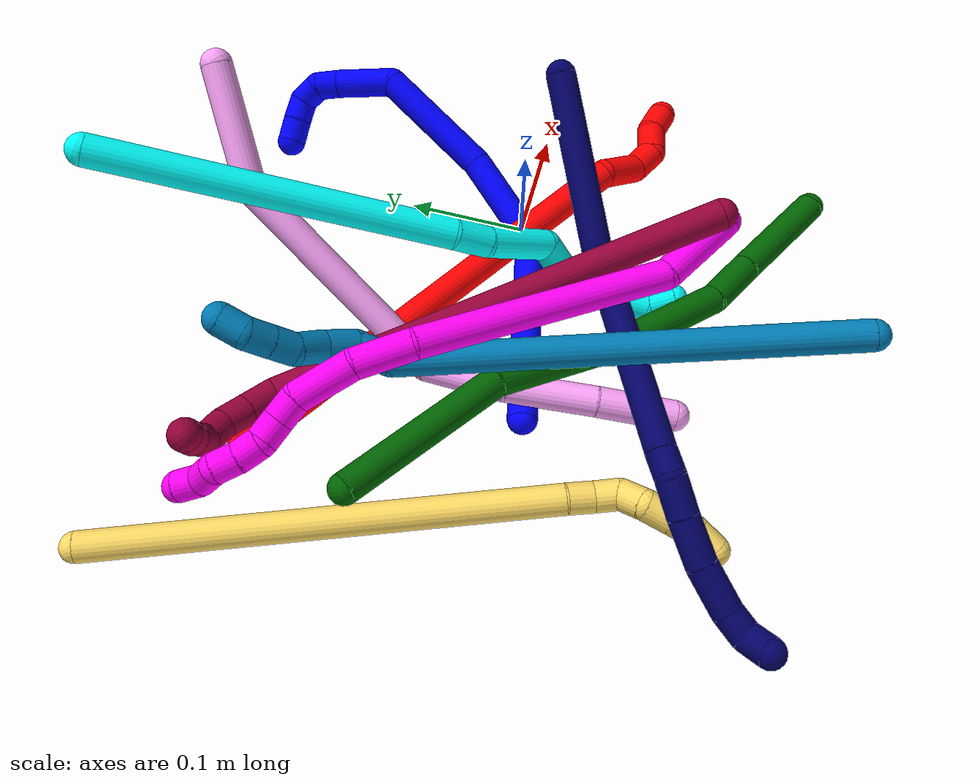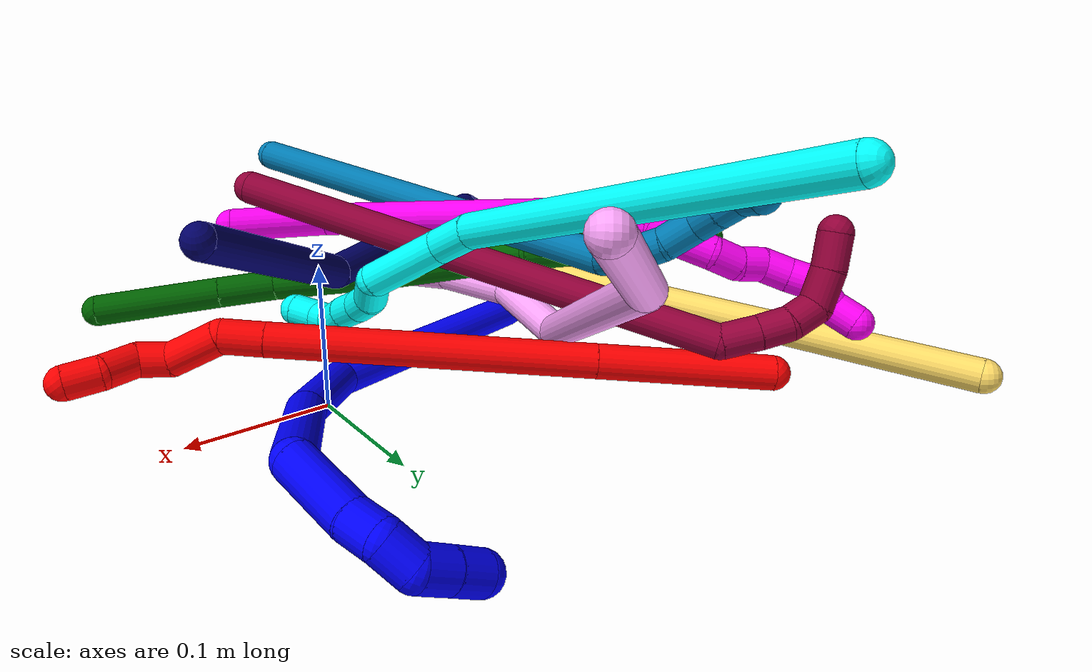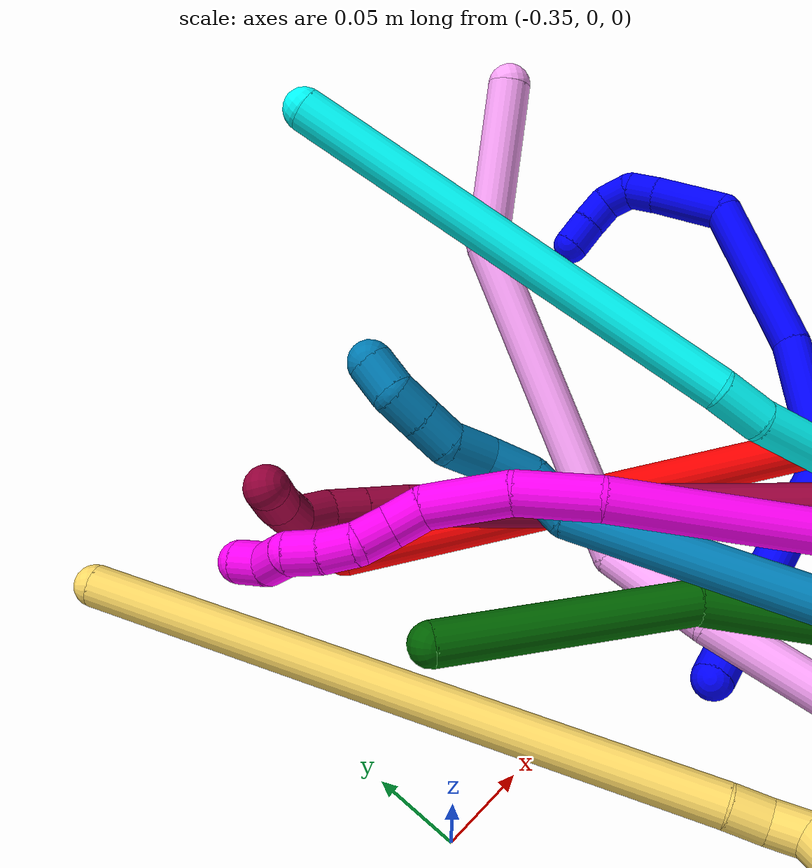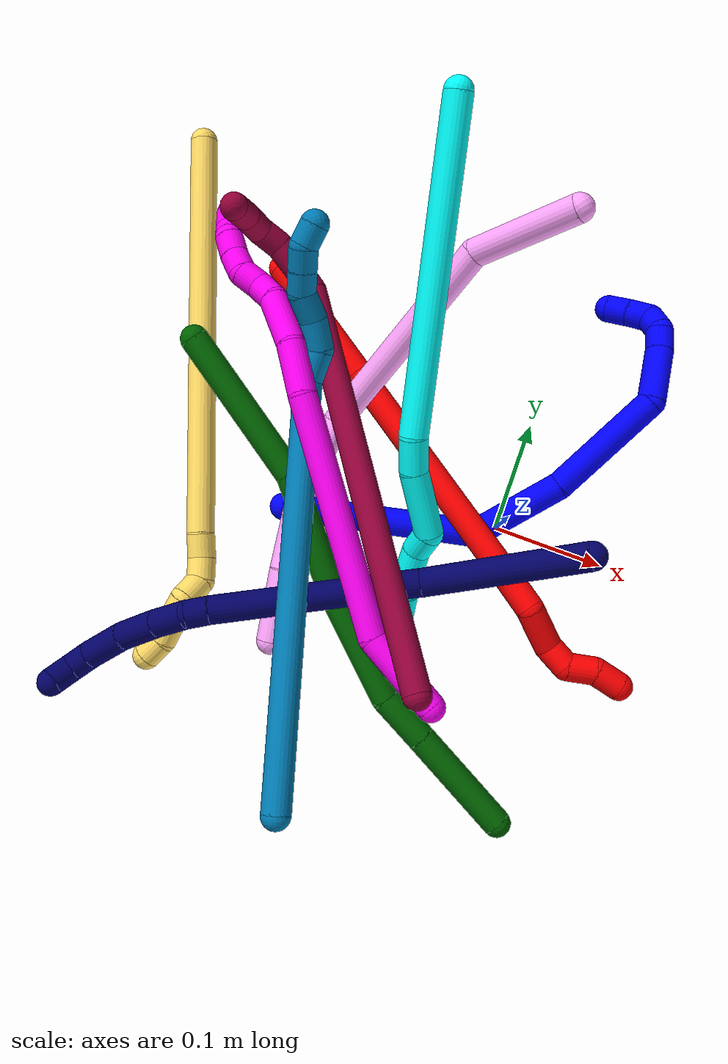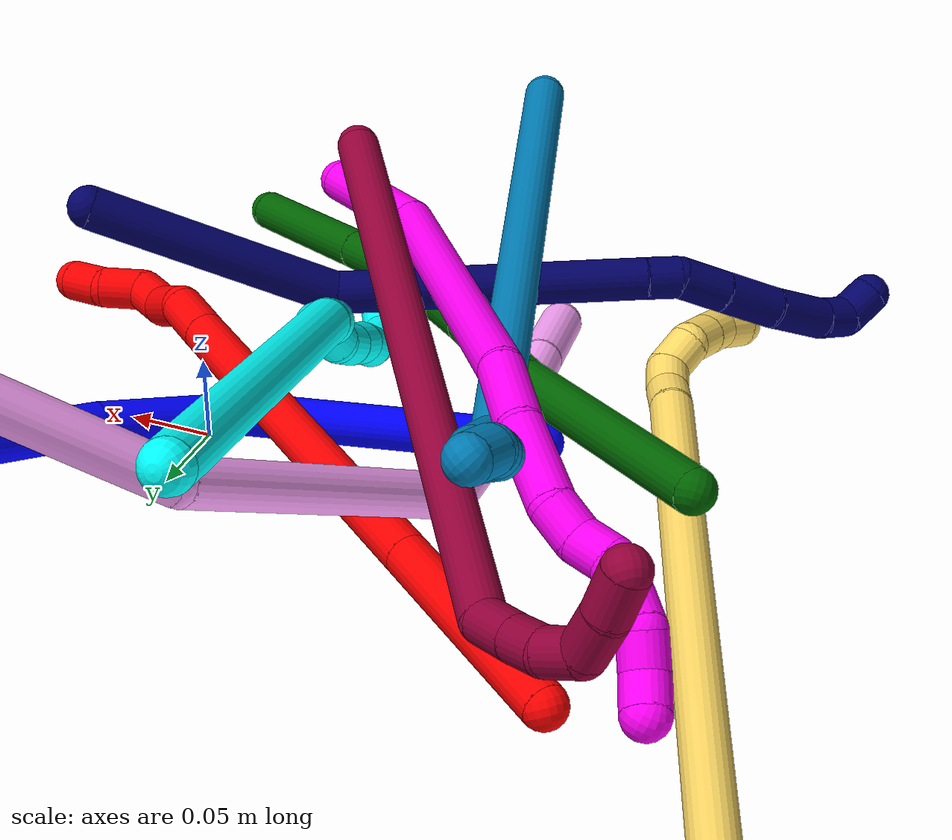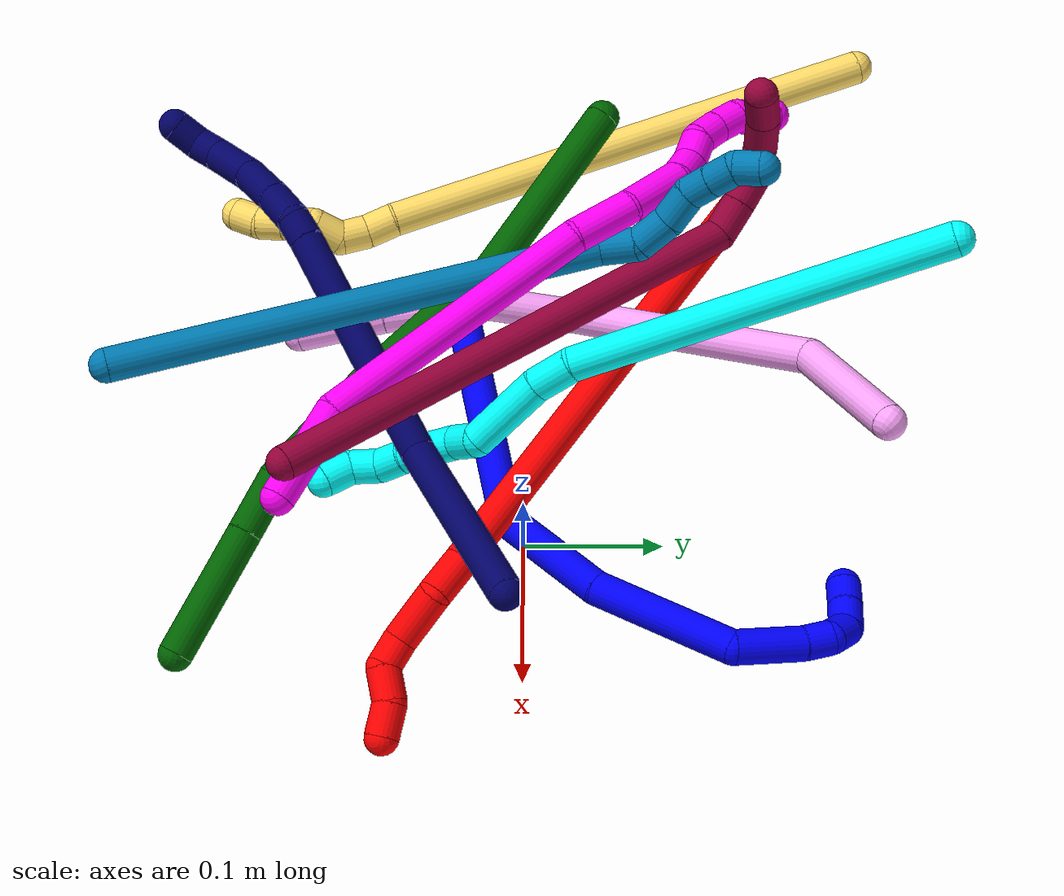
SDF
<sdf version="1.7">
 <world name="default">
  <plugin name="TubeGeneratorPlugin" filename="libtube_generator_plugin.so"/>
  <model name="photoneo_s_sensor">
   <static>1</static>
   <pose>0 0 2 1.57079 1.57079 3.14159</pose>
   <link name="link">
    <inertial><mass>0.1</mass></inertial>
    <sensor name="sensor" type="depth">
     <update_rate>30</update_rate>
     <camera>
      <horizontal_fov>1.22</horizontal_fov>
      <image><width>1920</width><height>1200</height><format>B8G8R8</format></image>
      <clip><near>0.1</near><far>4</far></clip>
      <depth_camera><output>points</output></depth_camera>
     </camera>
     <plugin name="camera_plugin" filename="libgazebo_ros_depth_camera.so">
      <baseline>0.2</baseline>
      <alwaysOn>1</alwaysOn>
      <updateRate>0.0</updateRate>
      <cameraName>camera_ir</cameraName>
      <imageTopicName>/camera/color/image_raw</imageTopicName>
      <cameraInfoTopicName>/camera/color/camera_info</cameraInfoTopicName>
      <depthImageTopicName>/camera/depth/image_raw</depthImageTopicName>
      <depthImageCameraInfoTopicName>/camera/depth/camera_info</depthImageCameraInfoTopicName>
      <pointCloudTopicName>/camera/depth/points</pointCloudTopicName>
      <frameName>fr_optical</frameName>
      <pointCloudCutoff>0.1</pointCloudCutoff>
      <pointCloudCutoffMax>2.0</pointCloudCutoffMax>
      <distortionK1>0</distortionK1>
      <distortionK2>0</distortionK2>
      <distortionK3>0</distortionK3>
      <distortionT1>0</distortionT1>
      <distortionT2>0</distortionT2>
      <CxPrime>0</CxPrime>
      <Cx>0</Cx>
      <Cy>0</Cy>
      <focalLength>0</focalLength>
      <hackBaseline>0</hackBaseline>
     </plugin>
    </sensor>
   </link>
  </model>
  <gravity>0 0 -9.8</gravity>
  <magnetic_field>6e-06 2.3e-05 -4.2e-05</magnetic_field>
  <atmosphere type="adiabatic"/>
  <physics name="default_physics" default="0" type="ode">
   <max_step_size>0.003</max_step_size>
   <real_time_factor>1</real_time_factor>
   <real_time_update_rate>1000</real_time_update_rate>
   <max_contacts>10000</max_contacts>
   <ode>
    <solver>
     <type>quick</type>
     <iters>100</iters>
     <sor>1.3</sor>
     <use_dynamic_moi_rescaling>0</use_dynamic_moi_rescaling>
    </solver>
    <constraints>
     <contact_max_correcting_vel>0</contact_max_correcting_vel>
     <contact_surface_layer>0.001</contact_surface_layer>
     <cfm>0</cfm>
     <erp>0.2</erp>
    </constraints>
   </ode>
  </physics>
  <scene><ambient>0.4 0.4 0.4 1</ambient><background>0.7 0.7 0.7 1</background><shadows>0</shadows></scene>
  <audio><device>default</device></audio>
  <spherical_coordinates>
   <surface_model>EARTH_WGS84</surface_model>
   <latitude_deg>0</latitude_deg>
   <longitude_deg>0</longitude_deg>
   <elevation>0</elevation>
   <heading_deg>0</heading_deg>
  </spherical_coordinates>
  <model name="bin">
   <static>1</static>
   <link name="bottom">
    <collision name="collision-bottom">
     <pose>0 0 -0.01 0 -0 0</pose>
     <geometry><box><size>0.8 0.6 0.02</size></box></geometry>
     <surface>
      <friction><ode><mu>100</mu><mu2>100</mu2></ode></friction>
      <contact><collide_bitmask>65535</collide_bitmask></contact>
     </surface>
    </collision>
   </link>
   <link name="west_wall">
    <collision name="collision-west_wall">
     <pose>-0.41 0 0.1 0 -0 0</pose>
     <geometry><box><size>0.02 0.6 0.2</size></box></geometry>
     <surface>
      <friction><ode><mu>100</mu><mu2>100</mu2></ode></friction>
      <contact><collide_bitmask>65535</collide_bitmask></contact>
     </surface>
    </collision>
   </link>
   <link name="east_wall">
    <collision name="collision-east_wall">
     <pose>0.41 0 0.1 0 -0 0</pose>
     <geometry><box><size>0.02 0.6 0.2</size></box></geometry>
     <surface>
      <friction><ode><mu>100</mu><mu2>100</mu2></ode></friction>
      <contact><collide_bitmask>65535</collide_bitmask></contact>
     </surface>
    </collision>
   </link>
   <link name="south_wall">
    <collision name="collision-south_wall">
     <pose>0 -0.31 0.1 0 -0 0</pose>
     <geometry><box><size>0.8 0.02 0.2</size></box></geometry>
     <surface>
      <friction><ode><mu>100</mu><mu2>100</mu2></ode></friction>
      <contact><collide_bitmask>65535</collide_bitmask></contact>
     </surface>
    </collision>
   </link>
   <link name="north_wall">
    <collision name="collision-north_wall">
     <pose>0 0.31 0.1 0 -0 0</pose>
     <geometry><box><size>0.8 0.02 0.2</size></box></geometry>
     <surface>
      <friction><ode><mu>100</mu><mu2>100</mu2></ode></friction>
      <contact><collide_bitmask>65535</collide_bitmask></contact>
     </surface>
    </collision>
   </link>
  </model>
  <model name="1">
   <static>0</static>
   <link name="1">
    <collision name="collision-cylinder-e_1_1_4">
     <pose>0.072469 0.012462 -0.046433 -2.87939 0.985058 -2.65972</pose>
     <geometry><cylinder><radius>0.0125</radius><length>0.173933</length></cylinder></geometry>
     <surface>
      <friction><ode><mu>1.16</mu><mu2>1.16</mu2><slip1>0</slip1><slip2>0</slip2></ode></friction>
      <contact><ode><kp>1e+06</kp><kd>1</kd><max_vel>0</max_vel><min_depth>0.001</min_depth></ode></contact>
     </surface>
    </collision>
    <visual name="visual-cylinder-e_1_1_4">
     <pose>0.072469 0.012462 -0.046433 -2.87939 0.985058 -2.65972</pose>
     <geometry><cylinder><radius>0.0125</radius><length>0.173933</length></cylinder></geometry>
     <material><ambient>0 0 1 1</ambient></material>
    </visual>
    <collision name="collision-cylinder-e_2_4_5">
     <pose>0.174796 0.054861 -0.101504 -1.85169 0.764071 -0.981082</pose>
     <geometry><cylinder><radius>0.0125</radius><length>0.08631</length></cylinder></geometry>
     <surface>
      <friction><ode><mu>1.16</mu><mu2>1.16</mu2><slip1>0</slip1><slip2>0</slip2></ode></friction>
      <contact><ode><kp>1e+06</kp><kd>1</kd><max_vel>0</max_vel><min_depth>0.001</min_depth></ode></contact>
     </surface>
    </collision>
    <visual name="visual-cylinder-e_2_4_5">
     <pose>0.174796 0.054861 -0.101504 -1.85169 0.764071 -0.981082</pose>
     <geometry><cylinder><radius>0.0125</radius><length>0.08631</length></cylinder></geometry>
     <material><ambient>0 0 1 1</ambient></material>
    </visual>
    <collision name="collision-cylinder-e_3_5_6">
     <pose>0.234532 0.129697 -0.114657 -1.67102 0.584851 -0.642629</pose>
     <geometry><cylinder><radius>0.0125</radius><length>0.108239</length></cylinder></geometry>
     <surface>
      <friction><ode><mu>1.16</mu><mu2>1.16</mu2><slip1>0</slip1><slip2>0</slip2></ode></friction>
      <contact><ode><kp>1e+06</kp><kd>1</kd><max_vel>0</max_vel><min_depth>0.001</min_depth></ode></contact>
     </surface>
    </collision>
    <visual name="visual-cylinder-e_3_5_6">
     <pose>0.234532 0.129697 -0.114657 -1.67102 0.584851 -0.642629</pose>
     <geometry><cylinder><radius>0.0125</radius><length>0.108239</length></cylinder></geometry>
     <material><ambient>0 0 1 1</ambient></material>
    </visual>
    <collision name="collision-cylinder-e_4_6_7">
     <pose>0.260315 0.199475 -0.123147 -1.72923 -0.161099 0.188729</pose>
     <geometry><cylinder><radius>0.0125</radius><length>0.051052</length></cylinder></geometry>
     <surface>
      <friction><ode><mu>1.16</mu><mu2>1.16</mu2><slip1>0</slip1><slip2>0</slip2></ode></friction>
      <contact><ode><kp>1e+06</kp><kd>1</kd><max_vel>0</max_vel><min_depth>0.001</min_depth></ode></contact>
     </surface>
    </collision>
    <visual name="visual-cylinder-e_4_6_7">
     <pose>0.260315 0.199475 -0.123147 -1.72923 -0.161099 0.188729</pose>
     <geometry><cylinder><radius>0.0125</radius><length>0.051052</length></cylinder></geometry>
     <material><ambient>0 0 1 1</ambient></material>
    </visual>
    <collision name="collision-cylinder-e_5_7_8">
     <pose>0.253633 0.234083 -0.127484 -1.60802 -0.25982 0.26956</pose>
     <geometry><cylinder><radius>0.0125</radius><length>0.020144</length></cylinder></geometry>
     <surface>
      <friction><ode><mu>1.16</mu><mu2>1.16</mu2><slip1>0</slip1><slip2>0</slip2></ode></friction>
      <contact><ode><kp>1e+06</kp><kd>1</kd><max_vel>0</max_vel><min_depth>0.001</min_depth></ode></contact>
     </surface>
    </collision>
    <visual name="visual-cylinder-e_5_7_8">
     <pose>0.253633 0.234083 -0.127484 -1.60802 -0.25982 0.26956</pose>
     <geometry><cylinder><radius>0.0125</radius><length>0.020144</length></cylinder></geometry>
     <material><ambient>0 0 1 1</ambient></material>
    </visual>
    <collision name="collision-cylinder-e_6_8_9">
     <pose>0.243856 0.250204 -0.130674 -1.98708 -0.799355 1.1508</pose>
     <geometry><cylinder><radius>0.0125</radius><length>0.020058</length></cylinder></geometry>
     <surface>
      <friction><ode><mu>1.16</mu><mu2>1.16</mu2><slip1>0</slip1><slip2>0</slip2></ode></friction>
      <contact><ode><kp>1e+06</kp><kd>1</kd><max_vel>0</max_vel><min_depth>0.001</min_depth></ode></contact>
     </surface>
    </collision>
    <visual name="visual-cylinder-e_6_8_9">
     <pose>0.243856 0.250204 -0.130674 -1.98708 -0.799355 1.1508</pose>
     <geometry><cylinder><radius>0.0125</radius><length>0.020058</length></cylinder></geometry>
     <material><ambient>0 0 1 1</ambient></material>
    </visual>
    <collision name="collision-cylinder-e_7_9_10">
     <pose>0.226782 0.25774 -0.132273 -0.748848 -1.40285 0.641</pose>
     <geometry><cylinder><radius>0.0125</radius><length>0.020051</length></cylinder></geometry>
     <surface>
      <friction><ode><mu>1.16</mu><mu2>1.16</mu2><slip1>0</slip1><slip2>0</slip2></ode></friction>
      <contact><ode><kp>1e+06</kp><kd>1</kd><max_vel>0</max_vel><min_depth>0.001</min_depth></ode></contact>
     </surface>
    </collision>
    <visual name="visual-cylinder-e_7_9_10">
     <pose>0.226782 0.25774 -0.132273 -0.748848 -1.40285 0.641</pose>
     <geometry><cylinder><radius>0.0125</radius><length>0.020051</length></cylinder></geometry>
     <material><ambient>0 0 1 1</ambient></material>
    </visual>
    <collision name="collision-cylinder-e_8_10_2">
     <pose>0.206866 0.259624 -0.130064 -0.647771 -1.44864 0.577431</pose>
     <geometry><cylinder><radius>0.0125</radius><length>0.020213</length></cylinder></geometry>
     <surface>
      <friction><ode><mu>1.16</mu><mu2>1.16</mu2><slip1>0</slip1><slip2>0</slip2></ode></friction>
      <contact><ode><kp>1e+06</kp><kd>1</kd><max_vel>0</max_vel><min_depth>0.001</min_depth></ode></contact>
     </surface>
    </collision>
    <visual name="visual-cylinder-e_8_10_2">
     <pose>0.206866 0.259624 -0.130064 -0.647771 -1.44864 0.577431</pose>
     <geometry><cylinder><radius>0.0125</radius><length>0.020213</length></cylinder></geometry>
     <material><ambient>0 0 1 1</ambient></material>
    </visual>
    <collision name="collision-sphere-2">
     <pose>0.196834 0.260367 -0.129082 0 -0 0</pose>
     <geometry><sphere><radius>0.0125</radius></sphere></geometry>
     <surface>
      <friction><ode><mu>1.16</mu><mu2>1.16</mu2><slip1>0</slip1><slip2>0</slip2></ode></friction>
      <contact><ode><kp>1e+06</kp><kd>1</kd><max_vel>0</max_vel><min_depth>0.001</min_depth></ode></contact>
     </surface>
    </collision>
    <visual name="visual-sphere-2">
     <pose>0.196834 0.260367 -0.129082 0 -0 0</pose>
     <geometry><sphere><radius>0.0125</radius></sphere></geometry>
     <material><ambient>0 0 1 1</ambient></material>
    </visual>
    <collision name="collision-sphere-10">
     <pose>0.216897 0.258881 -0.131046 0 -0 0</pose>
     <geometry><sphere><radius>0.0125</radius></sphere></geometry>
     <surface>
      <friction><ode><mu>1.16</mu><mu2>1.16</mu2><slip1>0</slip1><slip2>0</slip2></ode></friction>
      <contact><ode><kp>1e+06</kp><kd>1</kd><max_vel>0</max_vel><min_depth>0.001</min_depth></ode></contact>
     </surface>
    </collision>
    <visual name="visual-sphere-10">
     <pose>0.216897 0.258881 -0.131046 0 -0 0</pose>
     <geometry><sphere><radius>0.0125</radius></sphere></geometry>
     <material><ambient>0 0 1 1</ambient></material>
    </visual>
    <collision name="collision-sphere-9">
     <pose>0.236666 0.256599 -0.133501 0 -0 0</pose>
     <geometry><sphere><radius>0.0125</radius></sphere></geometry>
     <surface>
      <friction><ode><mu>1.16</mu><mu2>1.16</mu2><slip1>0</slip1><slip2>0</slip2></ode></friction>
      <contact><ode><kp>1e+06</kp><kd>1</kd><max_vel>0</max_vel><min_depth>0.001</min_depth></ode></contact>
     </surface>
    </collision>
    <visual name="visual-sphere-9">
     <pose>0.236666 0.256599 -0.133501 0 -0 0</pose>
     <geometry><sphere><radius>0.0125</radius></sphere></geometry>
     <material><ambient>0 0 1 1</ambient></material>
    </visual>
    <collision name="collision-sphere-4">
     <pose>0.144939 0.024924 -0.092866 0 -0 0</pose>
     <geometry><sphere><radius>0.0125</radius></sphere></geometry>
     <surface>
      <friction><ode><mu>1.16</mu><mu2>1.16</mu2><slip1>0</slip1><slip2>0</slip2></ode></friction>
      <contact><ode><kp>1e+06</kp><kd>1</kd><max_vel>0</max_vel><min_depth>0.001</min_depth></ode></contact>
     </surface>
    </collision>
    <visual name="visual-sphere-4">
     <pose>0.144939 0.024924 -0.092866 0 -0 0</pose>
     <geometry><sphere><radius>0.0125</radius></sphere></geometry>
     <material><ambient>0 0 1 1</ambient></material>
    </visual>
    <collision name="collision-sphere-1">
     <geometry><sphere><radius>0.0125</radius></sphere></geometry>
     <surface>
      <friction><ode><mu>1.16</mu><mu2>1.16</mu2><slip1>0</slip1><slip2>0</slip2></ode></friction>
      <contact><ode><kp>1e+06</kp><kd>1</kd><max_vel>0</max_vel><min_depth>0.001</min_depth></ode></contact>
     </surface>
    </collision>
    <visual name="visual-sphere-1">
     <geometry><sphere><radius>0.0125</radius></sphere></geometry>
     <material><ambient>0 0 1 1</ambient></material>
    </visual>
    <collision name="collision-sphere-8">
     <pose>0.251046 0.24381 -0.127846 0 -0 0</pose>
     <geometry><sphere><radius>0.0125</radius></sphere></geometry>
     <surface>
      <friction><ode><mu>1.16</mu><mu2>1.16</mu2><slip1>0</slip1><slip2>0</slip2></ode></friction>
      <contact><ode><kp>1e+06</kp><kd>1</kd><max_vel>0</max_vel><min_depth>0.001</min_depth></ode></contact>
     </surface>
    </collision>
    <visual name="visual-sphere-8">
     <pose>0.251046 0.24381 -0.127846 0 -0 0</pose>
     <geometry><sphere><radius>0.0125</radius></sphere></geometry>
     <material><ambient>0 0 1 1</ambient></material>
    </visual>
    <collision name="collision-sphere-5">
     <pose>0.204654 0.084799 -0.110142 0 -0 0</pose>
     <geometry><sphere><radius>0.0125</radius></sphere></geometry>
     <surface>
      <friction><ode><mu>1.16</mu><mu2>1.16</mu2><slip1>0</slip1><slip2>0</slip2></ode></friction>
      <contact><ode><kp>1e+06</kp><kd>1</kd><max_vel>0</max_vel><min_depth>0.001</min_depth></ode></contact>
     </surface>
    </collision>
    <visual name="visual-sphere-5">
     <pose>0.204654 0.084799 -0.110142 0 -0 0</pose>
     <geometry><sphere><radius>0.0125</radius></sphere></geometry>
     <material><ambient>0 0 1 1</ambient></material>
    </visual>
    <collision name="collision-sphere-6">
     <pose>0.26441 0.174595 -0.119172 0 -0 0</pose>
     <geometry><sphere><radius>0.0125</radius></sphere></geometry>
     <surface>
      <friction><ode><mu>1.16</mu><mu2>1.16</mu2><slip1>0</slip1><slip2>0</slip2></ode></friction>
      <contact><ode><kp>1e+06</kp><kd>1</kd><max_vel>0</max_vel><min_depth>0.001</min_depth></ode></contact>
     </surface>
    </collision>
    <visual name="visual-sphere-6">
     <pose>0.26441 0.174595 -0.119172 0 -0 0</pose>
     <geometry><sphere><radius>0.0125</radius></sphere></geometry>
     <material><ambient>0 0 1 1</ambient></material>
    </visual>
    <collision name="collision-sphere-7">
     <pose>0.256221 0.224355 -0.127122 0 -0 0</pose>
     <geometry><sphere><radius>0.0125</radius></sphere></geometry>
     <surface>
      <friction><ode><mu>1.16</mu><mu2>1.16</mu2><slip1>0</slip1><slip2>0</slip2></ode></friction>
      <contact><ode><kp>1e+06</kp><kd>1</kd><max_vel>0</max_vel><min_depth>0.001</min_depth></ode></contact>
     </surface>
    </collision>
    <visual name="visual-sphere-7">
     <pose>0.256221 0.224355 -0.127122 0 -0 0</pose>
     <geometry><sphere><radius>0.0125</radius></sphere></geometry>
     <material><ambient>0 0 1 1</ambient></material>
    </visual>
    <inertial>
     <pose>0.170191 0.102549 -0.092009 0 -0 0</pose>
     <mass>0.5</mass>
     <inertia>
      <ixx>-0.000291</ixx>
      <ixy>0</ixy>
      <ixz>0</ixz>
      <iyy>0.000299</iyy>
      <iyz>0</iyz>
      <izz>-0.000685</izz>
     </inertia>
    </inertial>
   </link>
   <pose>-0.186627 -0.047451 0.011489 0.013098 -0.568216 0.05621</pose>
  </model>
  <model name="2">
   <static>0</static>
   <link name="2">
    <collision name="collision-cylinder-e_1_1_4">
     <pose>0.024957 -0.03979 -0.041198 2.37357 0.41092 0.95234</pose>
     <geometry><cylinder><radius>0.0125</radius><length>0.124954</length></cylinder></geometry>
     <surface>
      <friction><ode><mu>1.16</mu><mu2>1.16</mu2><slip1>0</slip1><slip2>0</slip2></ode></friction>
      <contact><ode><kp>1e+06</kp><kd>1</kd><max_vel>0</max_vel><min_depth>0.001</min_depth></ode></contact>
     </surface>
    </collision>
    <visual name="visual-cylinder-e_1_1_4">
     <pose>0.024957 -0.03979 -0.041198 2.37357 0.41092 0.95234</pose>
     <geometry><cylinder><radius>0.0125</radius><length>0.124954</length></cylinder></geometry>
     <material><ambient>1 0 0 1</ambient></material>
    </visual>
    <collision name="collision-cylinder-e_2_4_5">
     <pose>0.09571 -0.152585 -0.157852 2.37271 0.411314 0.952135</pose>
     <geometry><cylinder><radius>0.0125</radius><length>0.229089</length></cylinder></geometry>
     <surface>
      <friction><ode><mu>1.16</mu><mu2>1.16</mu2><slip1>0</slip1><slip2>0</slip2></ode></friction>
      <contact><ode><kp>1e+06</kp><kd>1</kd><max_vel>0</max_vel><min_depth>0.001</min_depth></ode></contact>
     </surface>
    </collision>
    <visual name="visual-cylinder-e_2_4_5">
     <pose>0.09571 -0.152585 -0.157852 2.37271 0.411314 0.952135</pose>
     <geometry><cylinder><radius>0.0125</radius><length>0.229089</length></cylinder></geometry>
     <material><ambient>1 0 0 1</ambient></material>
    </visual>
    <collision name="collision-cylinder-e_3_5_6">
     <pose>0.147825 -0.235201 -0.243484 2.38472 0.423989 0.992309</pose>
     <geometry><cylinder><radius>0.0125</radius><length>0.030717</length></cylinder></geometry>
     <surface>
      <friction><ode><mu>1.16</mu><mu2>1.16</mu2><slip1>0</slip1><slip2>0</slip2></ode></friction>
      <contact><ode><kp>1e+06</kp><kd>1</kd><max_vel>0</max_vel><min_depth>0.001</min_depth></ode></contact>
     </surface>
    </collision>
    <visual name="visual-cylinder-e_3_5_6">
     <pose>0.147825 -0.235201 -0.243484 2.38472 0.423989 0.992309</pose>
     <geometry><cylinder><radius>0.0125</radius><length>0.030717</length></cylinder></geometry>
     <material><ambient>1 0 0 1</ambient></material>
    </visual>
    <collision name="collision-cylinder-e_4_6_7">
     <pose>0.167466 -0.260216 -0.257243 1.79923 0.700092 0.861778</pose>
     <geometry><cylinder><radius>0.0125</radius><length>0.041357</length></cylinder></geometry>
     <surface>
      <friction><ode><mu>1.16</mu><mu2>1.16</mu2><slip1>0</slip1><slip2>0</slip2></ode></friction>
      <contact><ode><kp>1e+06</kp><kd>1</kd><max_vel>0</max_vel><min_depth>0.001</min_depth></ode></contact>
     </surface>
    </collision>
    <visual name="visual-cylinder-e_4_6_7">
     <pose>0.167466 -0.260216 -0.257243 1.79923 0.700092 0.861778</pose>
     <geometry><cylinder><radius>0.0125</radius><length>0.041357</length></cylinder></geometry>
     <material><ambient>1 0 0 1</ambient></material>
    </visual>
    <collision name="collision-cylinder-e_5_7_8">
     <pose>0.184645 -0.283928 -0.268107 2.29059 0.335754 0.715713</pose>
     <geometry><cylinder><radius>0.0125</radius><length>0.023402</length></cylinder></geometry>
     <surface>
      <friction><ode><mu>1.16</mu><mu2>1.16</mu2><slip1>0</slip1><slip2>0</slip2></ode></friction>
      <contact><ode><kp>1e+06</kp><kd>1</kd><max_vel>0</max_vel><min_depth>0.001</min_depth></ode></contact>
     </surface>
    </collision>
    <visual name="visual-cylinder-e_5_7_8">
     <pose>0.184645 -0.283928 -0.268107 2.29059 0.335754 0.715713</pose>
     <geometry><cylinder><radius>0.0125</radius><length>0.023402</length></cylinder></geometry>
     <material><ambient>1 0 0 1</ambient></material>
    </visual>
    <collision name="collision-cylinder-e_6_8_9">
     <pose>0.185044 -0.303871 -0.279476 1.90853 -0.273221 -0.383191</pose>
     <geometry><cylinder><radius>0.0125</radius><length>0.025615</length></cylinder></geometry>
     <surface>
      <friction><ode><mu>1.16</mu><mu2>1.16</mu2><slip1>0</slip1><slip2>0</slip2></ode></friction>
      <contact><ode><kp>1e+06</kp><kd>1</kd><max_vel>0</max_vel><min_depth>0.001</min_depth></ode></contact>
     </surface>
    </collision>
    <visual name="visual-cylinder-e_6_8_9">
     <pose>0.185044 -0.303871 -0.279476 1.90853 -0.273221 -0.383191</pose>
     <geometry><cylinder><radius>0.0125</radius><length>0.025615</length></cylinder></geometry>
     <material><ambient>1 0 0 1</ambient></material>
    </visual>
    <collision name="collision-cylinder-e_7_9_2">
     <pose>0.183385 -0.32667 -0.288732 2.00446 0.145043 0.22643</pose>
     <geometry><cylinder><radius>0.0125</radius><length>0.024865</length></cylinder></geometry>
     <surface>
      <friction><ode><mu>1.16</mu><mu2>1.16</mu2><slip1>0</slip1><slip2>0</slip2></ode></friction>
      <contact><ode><kp>1e+06</kp><kd>1</kd><max_vel>0</max_vel><min_depth>0.001</min_depth></ode></contact>
     </surface>
    </collision>
    <visual name="visual-cylinder-e_7_9_2">
     <pose>0.183385 -0.32667 -0.288732 2.00446 0.145043 0.22643</pose>
     <geometry><cylinder><radius>0.0125</radius><length>0.024865</length></cylinder></geometry>
     <material><ambient>1 0 0 1</ambient></material>
    </visual>
    <collision name="collision-sphere-2">
     <pose>0.185182 -0.337833 -0.293901 0 -0 0</pose>
     <geometry><sphere><radius>0.0125</radius></sphere></geometry>
     <surface>
      <friction><ode><mu>1.16</mu><mu2>1.16</mu2><slip1>0</slip1><slip2>0</slip2></ode></friction>
      <contact><ode><kp>1e+06</kp><kd>1</kd><max_vel>0</max_vel><min_depth>0.001</min_depth></ode></contact>
     </surface>
    </collision>
    <visual name="visual-sphere-2">
     <pose>0.185182 -0.337833 -0.293901 0 -0 0</pose>
     <geometry><sphere><radius>0.0125</radius></sphere></geometry>
     <material><ambient>1 0 0 1</ambient></material>
    </visual>
    <collision name="collision-sphere-9">
     <pose>0.181588 -0.315507 -0.283563 0 -0 0</pose>
     <geometry><sphere><radius>0.0125</radius></sphere></geometry>
     <surface>
      <friction><ode><mu>1.16</mu><mu2>1.16</mu2><slip1>0</slip1><slip2>0</slip2></ode></friction>
      <contact><ode><kp>1e+06</kp><kd>1</kd><max_vel>0</max_vel><min_depth>0.001</min_depth></ode></contact>
     </surface>
    </collision>
    <visual name="visual-sphere-9">
     <pose>0.181588 -0.315507 -0.283563 0 -0 0</pose>
     <geometry><sphere><radius>0.0125</radius></sphere></geometry>
     <material><ambient>1 0 0 1</ambient></material>
    </visual>
    <collision name="collision-sphere-4">
     <pose>0.049913 -0.079581 -0.082396 0 -0 0</pose>
     <geometry><sphere><radius>0.0125</radius></sphere></geometry>
     <surface>
      <friction><ode><mu>1.16</mu><mu2>1.16</mu2><slip1>0</slip1><slip2>0</slip2></ode></friction>
      <contact><ode><kp>1e+06</kp><kd>1</kd><max_vel>0</max_vel><min_depth>0.001</min_depth></ode></contact>
     </surface>
    </collision>
    <visual name="visual-sphere-4">
     <pose>0.049913 -0.079581 -0.082396 0 -0 0</pose>
     <geometry><sphere><radius>0.0125</radius></sphere></geometry>
     <material><ambient>1 0 0 1</ambient></material>
    </visual>
    <collision name="collision-sphere-1">
     <geometry><sphere><radius>0.0125</radius></sphere></geometry>
     <surface>
      <friction><ode><mu>1.16</mu><mu2>1.16</mu2><slip1>0</slip1><slip2>0</slip2></ode></friction>
      <contact><ode><kp>1e+06</kp><kd>1</kd><max_vel>0</max_vel><min_depth>0.001</min_depth></ode></contact>
     </surface>
    </collision>
    <visual name="visual-sphere-1">
     <geometry><sphere><radius>0.0125</radius></sphere></geometry>
     <material><ambient>1 0 0 1</ambient></material>
    </visual>
    <collision name="collision-sphere-8">
     <pose>0.1885 -0.292235 -0.27539 0 -0 0</pose>
     <geometry><sphere><radius>0.0125</radius></sphere></geometry>
     <surface>
      <friction><ode><mu>1.16</mu><mu2>1.16</mu2><slip1>0</slip1><slip2>0</slip2></ode></friction>
      <contact><ode><kp>1e+06</kp><kd>1</kd><max_vel>0</max_vel><min_depth>0.001</min_depth></ode></contact>
     </surface>
    </collision>
    <visual name="visual-sphere-8">
     <pose>0.1885 -0.292235 -0.27539 0 -0 0</pose>
     <geometry><sphere><radius>0.0125</radius></sphere></geometry>
     <material><ambient>1 0 0 1</ambient></material>
    </visual>
    <collision name="collision-sphere-5">
     <pose>0.141506 -0.225588 -0.233308 0 -0 0</pose>
     <geometry><sphere><radius>0.0125</radius></sphere></geometry>
     <surface>
      <friction><ode><mu>1.16</mu><mu2>1.16</mu2><slip1>0</slip1><slip2>0</slip2></ode></friction>
      <contact><ode><kp>1e+06</kp><kd>1</kd><max_vel>0</max_vel><min_depth>0.001</min_depth></ode></contact>
     </surface>
    </collision>
    <visual name="visual-sphere-5">
     <pose>0.141506 -0.225588 -0.233308 0 -0 0</pose>
     <geometry><sphere><radius>0.0125</radius></sphere></geometry>
     <material><ambient>1 0 0 1</ambient></material>
    </visual>
    <collision name="collision-sphere-6">
     <pose>0.154143 -0.244813 -0.253661 0 -0 0</pose>
     <geometry><sphere><radius>0.0125</radius></sphere></geometry>
     <surface>
      <friction><ode><mu>1.16</mu><mu2>1.16</mu2><slip1>0</slip1><slip2>0</slip2></ode></friction>
      <contact><ode><kp>1e+06</kp><kd>1</kd><max_vel>0</max_vel><min_depth>0.001</min_depth></ode></contact>
     </surface>
    </collision>
    <visual name="visual-sphere-6">
     <pose>0.154143 -0.244813 -0.253661 0 -0 0</pose>
     <geometry><sphere><radius>0.0125</radius></sphere></geometry>
     <material><ambient>1 0 0 1</ambient></material>
    </visual>
    <collision name="collision-sphere-7">
     <pose>0.180789 -0.27562 -0.260824 0 -0 0</pose>
     <geometry><sphere><radius>0.0125</radius></sphere></geometry>
     <surface>
      <friction><ode><mu>1.16</mu><mu2>1.16</mu2><slip1>0</slip1><slip2>0</slip2></ode></friction>
      <contact><ode><kp>1e+06</kp><kd>1</kd><max_vel>0</max_vel><min_depth>0.001</min_depth></ode></contact>
     </surface>
    </collision>
    <visual name="visual-sphere-7">
     <pose>0.180789 -0.27562 -0.260824 0 -0 0</pose>
     <geometry><sphere><radius>0.0125</radius></sphere></geometry>
     <material><ambient>1 0 0 1</ambient></material>
    </visual>
    <inertial>
     <pose>0.100264 -0.16093 -0.160081 0 -0 0</pose>
     <mass>0.5</mass>
     <inertia>
      <ixx>0.00154</ixx>
      <ixy>0</ixy>
      <ixz>0</ixz>
      <iyy>0.000637</iyy>
      <iyz>0</iyz>
      <izz>0.000264</izz>
     </inertia>
    </inertial>
   </link>
   <pose>-0.265407 0.160398 0.011487 2.63591 0.42303 -1.68916</pose>
  </model>
  <model name="3">
   <static>0</static>
   <link name="3">
    <collision name="collision-cylinder-e_1_1_4">
     <pose>-0.014552 -0.021199 -0.135371 2.98626 -0.105804 -1.19489</pose>
     <geometry><cylinder><radius>0.0125</radius><length>0.275583</length></cylinder></geometry>
     <surface>
      <friction><ode><mu>1.16</mu><mu2>1.16</mu2><slip1>0</slip1><slip2>0</slip2></ode></friction>
      <contact><ode><kp>1e+06</kp><kd>1</kd><max_vel>0</max_vel><min_depth>0.001</min_depth></ode></contact>
     </surface>
    </collision>
    <visual name="visual-cylinder-e_1_1_4">
     <pose>-0.014552 -0.021199 -0.135371 2.98626 -0.105804 -1.19489</pose>
     <geometry><cylinder><radius>0.0125</radius><length>0.275583</length></cylinder></geometry>
     <material><ambient>0.003922 1 0.996078 1</ambient></material>
    </visual>
    <collision name="collision-cylinder-e_2_4_5">
     <pose>-0.028537 -0.047863 -0.28484 2.77177 0.037448 0.199562</pose>
     <geometry><cylinder><radius>0.0125</radius><length>0.03026</length></cylinder></geometry>
     <surface>
      <friction><ode><mu>1.16</mu><mu2>1.16</mu2><slip1>0</slip1><slip2>0</slip2></ode></friction>
      <contact><ode><kp>1e+06</kp><kd>1</kd><max_vel>0</max_vel><min_depth>0.001</min_depth></ode></contact>
     </surface>
    </collision>
    <visual name="visual-cylinder-e_2_4_5">
     <pose>-0.028537 -0.047863 -0.28484 2.77177 0.037448 0.199562</pose>
     <geometry><cylinder><radius>0.0125</radius><length>0.03026</length></cylinder></geometry>
     <material><ambient>0.003922 1 0.996078 1</ambient></material>
    </visual>
    <collision name="collision-cylinder-e_3_5_6">
     <pose>-0.028746 -0.069501 -0.32383 2.56543 -0.026135 -0.088146</pose>
     <geometry><cylinder><radius>0.0125</radius><length>0.059391</length></cylinder></geometry>
     <surface>
      <friction><ode><mu>1.16</mu><mu2>1.16</mu2><slip1>0</slip1><slip2>0</slip2></ode></friction>
      <contact><ode><kp>1e+06</kp><kd>1</kd><max_vel>0</max_vel><min_depth>0.001</min_depth></ode></contact>
     </surface>
    </collision>
    <visual name="visual-cylinder-e_3_5_6">
     <pose>-0.028746 -0.069501 -0.32383 2.56543 -0.026135 -0.088146</pose>
     <geometry><cylinder><radius>0.0125</radius><length>0.059391</length></cylinder></geometry>
     <material><ambient>0.003922 1 0.996078 1</ambient></material>
    </visual>
    <collision name="collision-cylinder-e_4_6_7">
     <pose>-0.022462 -0.086523 -0.358967 3.05889 0.601806 2.87652</pose>
     <geometry><cylinder><radius>0.0125</radius><length>0.024942</length></cylinder></geometry>
     <surface>
      <friction><ode><mu>1.16</mu><mu2>1.16</mu2><slip1>0</slip1><slip2>0</slip2></ode></friction>
      <contact><ode><kp>1e+06</kp><kd>1</kd><max_vel>0</max_vel><min_depth>0.001</min_depth></ode></contact>
     </surface>
    </collision>
    <visual name="visual-cylinder-e_4_6_7">
     <pose>-0.022462 -0.086523 -0.358967 3.05889 0.601806 2.87652</pose>
     <geometry><cylinder><radius>0.0125</radius><length>0.024942</length></cylinder></geometry>
     <material><ambient>0.003922 1 0.996078 1</ambient></material>
    </visual>
    <collision name="collision-cylinder-e_5_7_8">
     <pose>-0.013422 -0.088651 -0.379231 3.01464 0.193626 1.9825</pose>
     <geometry><cylinder><radius>0.0125</radius><length>0.020584</length></cylinder></geometry>
     <surface>
      <friction><ode><mu>1.16</mu><mu2>1.16</mu2><slip1>0</slip1><slip2>0</slip2></ode></friction>
      <contact><ode><kp>1e+06</kp><kd>1</kd><max_vel>0</max_vel><min_depth>0.001</min_depth></ode></contact>
     </surface>
    </collision>
    <visual name="visual-cylinder-e_5_7_8">
     <pose>-0.013422 -0.088651 -0.379231 3.01464 0.193626 1.9825</pose>
     <geometry><cylinder><radius>0.0125</radius><length>0.020584</length></cylinder></geometry>
     <material><ambient>0.003922 1 0.996078 1</ambient></material>
    </visual>
    <collision name="collision-cylinder-e_6_8_9">
     <pose>-0.010393 -0.091656 -0.400787 2.99308 0.089628 1.08494</pose>
     <geometry><cylinder><radius>0.0125</radius><length>0.023426</length></cylinder></geometry>
     <surface>
      <friction><ode><mu>1.16</mu><mu2>1.16</mu2><slip1>0</slip1><slip2>0</slip2></ode></friction>
      <contact><ode><kp>1e+06</kp><kd>1</kd><max_vel>0</max_vel><min_depth>0.001</min_depth></ode></contact>
     </surface>
    </collision>
    <visual name="visual-cylinder-e_6_8_9">
     <pose>-0.010393 -0.091656 -0.400787 2.99308 0.089628 1.08494</pose>
     <geometry><cylinder><radius>0.0125</radius><length>0.023426</length></cylinder></geometry>
     <material><ambient>0.003922 1 0.996078 1</ambient></material>
    </visual>
    <collision name="collision-cylinder-e_7_9_10">
     <pose>-0.007133 -0.095966 -0.42294 2.90283 0.199737 1.39187</pose>
     <geometry><cylinder><radius>0.0125</radius><length>0.022293</length></cylinder></geometry>
     <surface>
      <friction><ode><mu>1.16</mu><mu2>1.16</mu2><slip1>0</slip1><slip2>0</slip2></ode></friction>
      <contact><ode><kp>1e+06</kp><kd>1</kd><max_vel>0</max_vel><min_depth>0.001</min_depth></ode></contact>
     </surface>
    </collision>
    <visual name="visual-cylinder-e_7_9_10">
     <pose>-0.007133 -0.095966 -0.42294 2.90283 0.199737 1.39187</pose>
     <geometry><cylinder><radius>0.0125</radius><length>0.022293</length></cylinder></geometry>
     <material><ambient>0.003922 1 0.996078 1</ambient></material>
    </visual>
    <collision name="collision-cylinder-e_8_10_11">
     <pose>-0.006884 -0.097296 -0.443897 -3.02098 -0.18622 1.99365</pose>
     <geometry><cylinder><radius>0.0125</radius><length>0.021202</length></cylinder></geometry>
     <surface>
      <friction><ode><mu>1.16</mu><mu2>1.16</mu2><slip1>0</slip1><slip2>0</slip2></ode></friction>
      <contact><ode><kp>1e+06</kp><kd>1</kd><max_vel>0</max_vel><min_depth>0.001</min_depth></ode></contact>
     </surface>
    </collision>
    <visual name="visual-cylinder-e_8_10_11">
     <pose>-0.006884 -0.097296 -0.443897 -3.02098 -0.18622 1.99365</pose>
     <geometry><cylinder><radius>0.0125</radius><length>0.021202</length></cylinder></geometry>
     <material><ambient>0.003922 1 0.996078 1</ambient></material>
    </visual>
    <collision name="collision-cylinder-e_9_11_2">
     <pose>-0.015348 -0.098371 -0.463005 2.88198 -0.6219 -2.36991</pose>
     <geometry><cylinder><radius>0.0125</radius><length>0.022319</length></cylinder></geometry>
     <surface>
      <friction><ode><mu>1.16</mu><mu2>1.16</mu2><slip1>0</slip1><slip2>0</slip2></ode></friction>
      <contact><ode><kp>1e+06</kp><kd>1</kd><max_vel>0</max_vel><min_depth>0.001</min_depth></ode></contact>
     </surface>
    </collision>
    <visual name="visual-cylinder-e_9_11_2">
     <pose>-0.015348 -0.098371 -0.463005 2.88198 -0.6219 -2.36991</pose>
     <geometry><cylinder><radius>0.0125</radius><length>0.022319</length></cylinder></geometry>
     <material><ambient>0.003922 1 0.996078 1</ambient></material>
    </visual>
    <collision name="collision-sphere-2">
     <pose>-0.021849 -0.100699 -0.471771 0 -0 0</pose>
     <geometry><sphere><radius>0.0125</radius></sphere></geometry>
     <surface>
      <friction><ode><mu>1.16</mu><mu2>1.16</mu2><slip1>0</slip1><slip2>0</slip2></ode></friction>
      <contact><ode><kp>1e+06</kp><kd>1</kd><max_vel>0</max_vel><min_depth>0.001</min_depth></ode></contact>
     </surface>
    </collision>
    <visual name="visual-sphere-2">
     <pose>-0.021849 -0.100699 -0.471771 0 -0 0</pose>
     <geometry><sphere><radius>0.0125</radius></sphere></geometry>
     <material><ambient>0.003922 1 0.996078 1</ambient></material>
    </visual>
    <collision name="collision-sphere-11">
     <pose>-0.008846 -0.096043 -0.454238 0 -0 0</pose>
     <geometry><sphere><radius>0.0125</radius></sphere></geometry>
     <surface>
      <friction><ode><mu>1.16</mu><mu2>1.16</mu2><slip1>0</slip1><slip2>0</slip2></ode></friction>
      <contact><ode><kp>1e+06</kp><kd>1</kd><max_vel>0</max_vel><min_depth>0.001</min_depth></ode></contact>
     </surface>
    </collision>
    <visual name="visual-sphere-11">
     <pose>-0.008846 -0.096043 -0.454238 0 -0 0</pose>
     <geometry><sphere><radius>0.0125</radius></sphere></geometry>
     <material><ambient>0.003922 1 0.996078 1</ambient></material>
    </visual>
    <collision name="collision-sphere-10">
     <pose>-0.004921 -0.098549 -0.433555 0 -0 0</pose>
     <geometry><sphere><radius>0.0125</radius></sphere></geometry>
     <surface>
      <friction><ode><mu>1.16</mu><mu2>1.16</mu2><slip1>0</slip1><slip2>0</slip2></ode></friction>
      <contact><ode><kp>1e+06</kp><kd>1</kd><max_vel>0</max_vel><min_depth>0.001</min_depth></ode></contact>
     </surface>
    </collision>
    <visual name="visual-sphere-10">
     <pose>-0.004921 -0.098549 -0.433555 0 -0 0</pose>
     <geometry><sphere><radius>0.0125</radius></sphere></geometry>
     <material><ambient>0.003922 1 0.996078 1</ambient></material>
    </visual>
    <collision name="collision-sphere-9">
     <pose>-0.009344 -0.093382 -0.412325 0 -0 0</pose>
     <geometry><sphere><radius>0.0125</radius></sphere></geometry>
     <surface>
      <friction><ode><mu>1.16</mu><mu2>1.16</mu2><slip1>0</slip1><slip2>0</slip2></ode></friction>
      <contact><ode><kp>1e+06</kp><kd>1</kd><max_vel>0</max_vel><min_depth>0.001</min_depth></ode></contact>
     </surface>
    </collision>
    <visual name="visual-sphere-9">
     <pose>-0.009344 -0.093382 -0.412325 0 -0 0</pose>
     <geometry><sphere><radius>0.0125</radius></sphere></geometry>
     <material><ambient>0.003922 1 0.996078 1</ambient></material>
    </visual>
    <collision name="collision-sphere-4">
     <pose>-0.029103 -0.042398 -0.270742 0 -0 0</pose>
     <geometry><sphere><radius>0.0125</radius></sphere></geometry>
     <surface>
      <friction><ode><mu>1.16</mu><mu2>1.16</mu2><slip1>0</slip1><slip2>0</slip2></ode></friction>
      <contact><ode><kp>1e+06</kp><kd>1</kd><max_vel>0</max_vel><min_depth>0.001</min_depth></ode></contact>
     </surface>
    </collision>
    <visual name="visual-sphere-4">
     <pose>-0.029103 -0.042398 -0.270742 0 -0 0</pose>
     <geometry><sphere><radius>0.0125</radius></sphere></geometry>
     <material><ambient>0.003922 1 0.996078 1</ambient></material>
    </visual>
    <collision name="collision-sphere-1">
     <geometry><sphere><radius>0.0125</radius></sphere></geometry>
     <surface>
      <friction><ode><mu>1.16</mu><mu2>1.16</mu2><slip1>0</slip1><slip2>0</slip2></ode></friction>
      <contact><ode><kp>1e+06</kp><kd>1</kd><max_vel>0</max_vel><min_depth>0.001</min_depth></ode></contact>
     </surface>
    </collision>
    <visual name="visual-sphere-1">
     <geometry><sphere><radius>0.0125</radius></sphere></geometry>
     <material><ambient>0.003922 1 0.996078 1</ambient></material>
    </visual>
    <collision name="collision-sphere-8">
     <pose>-0.011441 -0.089929 -0.389249 0 -0 0</pose>
     <geometry><sphere><radius>0.0125</radius></sphere></geometry>
     <surface>
      <friction><ode><mu>1.16</mu><mu2>1.16</mu2><slip1>0</slip1><slip2>0</slip2></ode></friction>
      <contact><ode><kp>1e+06</kp><kd>1</kd><max_vel>0</max_vel><min_depth>0.001</min_depth></ode></contact>
     </surface>
    </collision>
    <visual name="visual-sphere-8">
     <pose>-0.011441 -0.089929 -0.389249 0 -0 0</pose>
     <geometry><sphere><radius>0.0125</radius></sphere></geometry>
     <material><ambient>0.003922 1 0.996078 1</ambient></material>
    </visual>
    <collision name="collision-sphere-5">
     <pose>-0.02797 -0.053328 -0.298937 0 -0 0</pose>
     <geometry><sphere><radius>0.0125</radius></sphere></geometry>
     <surface>
      <friction><ode><mu>1.16</mu><mu2>1.16</mu2><slip1>0</slip1><slip2>0</slip2></ode></friction>
      <contact><ode><kp>1e+06</kp><kd>1</kd><max_vel>0</max_vel><min_depth>0.001</min_depth></ode></contact>
     </surface>
    </collision>
    <visual name="visual-sphere-5">
     <pose>-0.02797 -0.053328 -0.298937 0 -0 0</pose>
     <geometry><sphere><radius>0.0125</radius></sphere></geometry>
     <material><ambient>0.003922 1 0.996078 1</ambient></material>
    </visual>
    <collision name="collision-sphere-6">
     <pose>-0.029522 -0.085673 -0.348723 0 -0 0</pose>
     <geometry><sphere><radius>0.0125</radius></sphere></geometry>
     <surface>
      <friction><ode><mu>1.16</mu><mu2>1.16</mu2><slip1>0</slip1><slip2>0</slip2></ode></friction>
      <contact><ode><kp>1e+06</kp><kd>1</kd><max_vel>0</max_vel><min_depth>0.001</min_depth></ode></contact>
     </surface>
    </collision>
    <visual name="visual-sphere-6">
     <pose>-0.029522 -0.085673 -0.348723 0 -0 0</pose>
     <geometry><sphere><radius>0.0125</radius></sphere></geometry>
     <material><ambient>0.003922 1 0.996078 1</ambient></material>
    </visual>
    <collision name="collision-sphere-7">
     <pose>-0.015402 -0.087372 -0.369212 0 -0 0</pose>
     <geometry><sphere><radius>0.0125</radius></sphere></geometry>
     <surface>
      <friction><ode><mu>1.16</mu><mu2>1.16</mu2><slip1>0</slip1><slip2>0</slip2></ode></friction>
      <contact><ode><kp>1e+06</kp><kd>1</kd><max_vel>0</max_vel><min_depth>0.001</min_depth></ode></contact>
     </surface>
    </collision>
    <visual name="visual-sphere-7">
     <pose>-0.015402 -0.087372 -0.369212 0 -0 0</pose>
     <geometry><sphere><radius>0.0125</radius></sphere></geometry>
     <material><ambient>0.003922 1 0.996078 1</ambient></material>
    </visual>
    <inertial>
     <pose>-0.016617 -0.047892 -0.24096 0 -0 0</pose>
     <mass>0.5</mass>
     <inertia>
      <ixx>-0.000959</ixx>
      <ixy>0</ixy>
      <ixz>0</ixz>
      <iyy>-0.002252</iyy>
      <iyz>0</iyz>
      <izz>0.000431</izz>
     </inertia>
    </inertial>
   </link>
   <pose>-0.153023 0.288658 0.20189 0.94528 0.959977 2.63035</pose>
  </model>
  <model name="4">
   <static>0</static>
   <link name="4">
    <collision name="collision-cylinder-e_1_1_4">
     <pose>0.005808 0.022222 0.022075 -0.788719 0.183346 -0.076478</pose>
     <geometry><cylinder><radius>0.0125</radius><length>0.063713</length></cylinder></geometry>
     <surface>
      <friction><ode><mu>1.16</mu><mu2>1.16</mu2><slip1>0</slip1><slip2>0</slip2></ode></friction>
      <contact><ode><kp>1e+06</kp><kd>1</kd><max_vel>0</max_vel><min_depth>0.001</min_depth></ode></contact>
     </surface>
    </collision>
    <visual name="visual-cylinder-e_1_1_4">
     <pose>0.005808 0.022222 0.022075 -0.788719 0.183346 -0.076478</pose>
     <geometry><cylinder><radius>0.0125</radius><length>0.063713</length></cylinder></geometry>
     <material><ambient>1 0.65098 0.996078 1</ambient></material>
    </visual>
    <collision name="collision-cylinder-e_2_4_5">
     <pose>0.014452 0.070538 0.068873 -0.812358 0.078731 -0.033876</pose>
     <geometry><cylinder><radius>0.0125</radius><length>0.072116</length></cylinder></geometry>
     <surface>
      <friction><ode><mu>1.16</mu><mu2>1.16</mu2><slip1>0</slip1><slip2>0</slip2></ode></friction>
      <contact><ode><kp>1e+06</kp><kd>1</kd><max_vel>0</max_vel><min_depth>0.001</min_depth></ode></contact>
     </surface>
    </collision>
    <visual name="visual-cylinder-e_2_4_5">
     <pose>0.014452 0.070538 0.068873 -0.812358 0.078731 -0.033876</pose>
     <geometry><cylinder><radius>0.0125</radius><length>0.072116</length></cylinder></geometry>
     <material><ambient>1 0.65098 0.996078 1</ambient></material>
    </visual>
    <collision name="collision-cylinder-e_3_5_6">
     <pose>0.01163 0.12577 0.111494 -1.01998 -0.163966 0.091855</pose>
     <geometry><cylinder><radius>0.0125</radius><length>0.069322</length></cylinder></geometry>
     <surface>
      <friction><ode><mu>1.16</mu><mu2>1.16</mu2><slip1>0</slip1><slip2>0</slip2></ode></friction>
      <contact><ode><kp>1e+06</kp><kd>1</kd><max_vel>0</max_vel><min_depth>0.001</min_depth></ode></contact>
     </surface>
    </collision>
    <visual name="visual-cylinder-e_3_5_6">
     <pose>0.01163 0.12577 0.111494 -1.01998 -0.163966 0.091855</pose>
     <geometry><cylinder><radius>0.0125</radius><length>0.069322</length></cylinder></geometry>
     <material><ambient>1 0.65098 0.996078 1</ambient></material>
    </visual>
    <collision name="collision-cylinder-e_4_6_7">
     <pose>0.05038 0.240855 0.147373 -1.36456 0.468227 -0.38277</pose>
     <geometry><cylinder><radius>0.0125</radius><length>0.196795</length></cylinder></geometry>
     <surface>
      <friction><ode><mu>1.16</mu><mu2>1.16</mu2><slip1>0</slip1><slip2>0</slip2></ode></friction>
      <contact><ode><kp>1e+06</kp><kd>1</kd><max_vel>0</max_vel><min_depth>0.001</min_depth></ode></contact>
     </surface>
    </collision>
    <visual name="visual-cylinder-e_4_6_7">
     <pose>0.05038 0.240855 0.147373 -1.36456 0.468227 -0.38277</pose>
     <geometry><cylinder><radius>0.0125</radius><length>0.196795</length></cylinder></geometry>
     <material><ambient>1 0.65098 0.996078 1</ambient></material>
    </visual>
    <collision name="collision-cylinder-e_5_7_2">
     <pose>0.120227 0.365746 0.149871 -1.94918 0.545568 -0.782073</pose>
     <geometry><cylinder><radius>0.0125</radius><length>0.098053</length></cylinder></geometry>
     <surface>
      <friction><ode><mu>1.16</mu><mu2>1.16</mu2><slip1>0</slip1><slip2>0</slip2></ode></friction>
      <contact><ode><kp>1e+06</kp><kd>1</kd><max_vel>0</max_vel><min_depth>0.001</min_depth></ode></contact>
     </surface>
    </collision>
    <visual name="visual-cylinder-e_5_7_2">
     <pose>0.120227 0.365746 0.149871 -1.94918 0.545568 -0.782073</pose>
     <geometry><cylinder><radius>0.0125</radius><length>0.098053</length></cylinder></geometry>
     <material><ambient>1 0.65098 0.996078 1</ambient></material>
    </visual>
    <collision name="collision-sphere-2">
     <pose>0.145667 0.404691 0.134389 0 -0 0</pose>
     <geometry><sphere><radius>0.0125</radius></sphere></geometry>
     <surface>
      <friction><ode><mu>1.16</mu><mu2>1.16</mu2><slip1>0</slip1><slip2>0</slip2></ode></friction>
      <contact><ode><kp>1e+06</kp><kd>1</kd><max_vel>0</max_vel><min_depth>0.001</min_depth></ode></contact>
     </surface>
    </collision>
    <visual name="visual-sphere-2">
     <pose>0.145667 0.404691 0.134389 0 -0 0</pose>
     <geometry><sphere><radius>0.0125</radius></sphere></geometry>
     <material><ambient>1 0.65098 0.996078 1</ambient></material>
    </visual>
    <collision name="collision-sphere-7">
     <pose>0.094787 0.326801 0.165353 0 -0 0</pose>
     <geometry><sphere><radius>0.0125</radius></sphere></geometry>
     <surface>
      <friction><ode><mu>1.16</mu><mu2>1.16</mu2><slip1>0</slip1><slip2>0</slip2></ode></friction>
      <contact><ode><kp>1e+06</kp><kd>1</kd><max_vel>0</max_vel><min_depth>0.001</min_depth></ode></contact>
     </surface>
    </collision>
    <visual name="visual-sphere-7">
     <pose>0.094787 0.326801 0.165353 0 -0 0</pose>
     <geometry><sphere><radius>0.0125</radius></sphere></geometry>
     <material><ambient>1 0.65098 0.996078 1</ambient></material>
    </visual>
    <collision name="collision-sphere-6">
     <pose>0.005972 0.154908 0.129392 0 -0 0</pose>
     <geometry><sphere><radius>0.0125</radius></sphere></geometry>
     <surface>
      <friction><ode><mu>1.16</mu><mu2>1.16</mu2><slip1>0</slip1><slip2>0</slip2></ode></friction>
      <contact><ode><kp>1e+06</kp><kd>1</kd><max_vel>0</max_vel><min_depth>0.001</min_depth></ode></contact>
     </surface>
    </collision>
    <visual name="visual-sphere-6">
     <pose>0.005972 0.154908 0.129392 0 -0 0</pose>
     <geometry><sphere><radius>0.0125</radius></sphere></geometry>
     <material><ambient>1 0.65098 0.996078 1</ambient></material>
    </visual>
    <collision name="collision-sphere-5">
     <pose>0.017288 0.096631 0.093597 0 -0 0</pose>
     <geometry><sphere><radius>0.0125</radius></sphere></geometry>
     <surface>
      <friction><ode><mu>1.16</mu><mu2>1.16</mu2><slip1>0</slip1><slip2>0</slip2></ode></friction>
      <contact><ode><kp>1e+06</kp><kd>1</kd><max_vel>0</max_vel><min_depth>0.001</min_depth></ode></contact>
     </surface>
    </collision>
    <visual name="visual-sphere-5">
     <pose>0.017288 0.096631 0.093597 0 -0 0</pose>
     <geometry><sphere><radius>0.0125</radius></sphere></geometry>
     <material><ambient>1 0.65098 0.996078 1</ambient></material>
    </visual>
    <collision name="collision-sphere-1">
     <geometry><sphere><radius>0.0125</radius></sphere></geometry>
     <surface>
      <friction><ode><mu>1.16</mu><mu2>1.16</mu2><slip1>0</slip1><slip2>0</slip2></ode></friction>
      <contact><ode><kp>1e+06</kp><kd>1</kd><max_vel>0</max_vel><min_depth>0.001</min_depth></ode></contact>
     </surface>
    </collision>
    <visual name="visual-sphere-1">
     <geometry><sphere><radius>0.0125</radius></sphere></geometry>
     <material><ambient>1 0.65098 0.996078 1</ambient></material>
    </visual>
    <collision name="collision-sphere-4">
     <pose>0.011616 0.044444 0.044149 0 -0 0</pose>
     <geometry><sphere><radius>0.0125</radius></sphere></geometry>
     <surface>
      <friction><ode><mu>1.16</mu><mu2>1.16</mu2><slip1>0</slip1><slip2>0</slip2></ode></friction>
      <contact><ode><kp>1e+06</kp><kd>1</kd><max_vel>0</max_vel><min_depth>0.001</min_depth></ode></contact>
     </surface>
    </collision>
    <visual name="visual-sphere-4">
     <pose>0.011616 0.044444 0.044149 0 -0 0</pose>
     <geometry><sphere><radius>0.0125</radius></sphere></geometry>
     <material><ambient>1 0.65098 0.996078 1</ambient></material>
    </visual>
    <inertial>
     <pose>0.047843 0.196966 0.1156 0 -0 0</pose>
     <mass>0.5</mass>
     <inertia>
      <ixx>0.000417</ixx>
      <ixy>0</ixy>
      <ixz>0</ixz>
      <iyy>5.9e-05</iyy>
      <iyz>0</iyz>
      <izz>-0.001018</izz>
     </inertia>
    </inertial>
   </link>
   <pose>-0.155344 -0.163373 0.019619 2.39732 -1.50356 -3.03477</pose>
  </model>
  <model name="5">
   <static>0</static>
   <link name="5">
    <collision name="collision-cylinder-e_1_1_4">
     <pose>0.056867 -0.056515 -0.167977 2.81704 0.310488 1.52577</pose>
     <geometry><cylinder><radius>0.0125</radius><length>0.372258</length></cylinder></geometry>
     <surface>
      <friction><ode><mu>1.16</mu><mu2>1.16</mu2><slip1>0</slip1><slip2>0</slip2></ode></friction>
      <contact><ode><kp>1e+06</kp><kd>1</kd><max_vel>0</max_vel><min_depth>0.001</min_depth></ode></contact>
     </surface>
    </collision>
    <visual name="visual-cylinder-e_1_1_4">
     <pose>0.056867 -0.056515 -0.167977 2.81704 0.310488 1.52577</pose>
     <geometry><cylinder><radius>0.0125</radius><length>0.372258</length></cylinder></geometry>
     <material><ambient>1 0.858824 0.4 1</ambient></material>
    </visual>
    <collision name="collision-cylinder-e_2_4_5">
     <pose>0.11545 -0.116902 -0.346229 2.7812 0.155083 0.806282</pose>
     <geometry><cylinder><radius>0.0125</radius><length>0.022227</length></cylinder></geometry>
     <surface>
      <friction><ode><mu>1.16</mu><mu2>1.16</mu2><slip1>0</slip1><slip2>0</slip2></ode></friction>
      <contact><ode><kp>1e+06</kp><kd>1</kd><max_vel>0</max_vel><min_depth>0.001</min_depth></ode></contact>
     </surface>
    </collision>
    <visual name="visual-cylinder-e_2_4_5">
     <pose>0.11545 -0.116902 -0.346229 2.7812 0.155083 0.806282</pose>
     <geometry><cylinder><radius>0.0125</radius><length>0.022227</length></cylinder></geometry>
     <material><ambient>1 0.858824 0.4 1</ambient></material>
    </visual>
    <collision name="collision-cylinder-e_3_5_6">
     <pose>0.121416 -0.123637 -0.365487 2.83303 0.423376 1.88876</pose>
     <geometry><cylinder><radius>0.0125</radius><length>0.020685</length></cylinder></geometry>
     <surface>
      <friction><ode><mu>1.16</mu><mu2>1.16</mu2><slip1>0</slip1><slip2>0</slip2></ode></friction>
      <contact><ode><kp>1e+06</kp><kd>1</kd><max_vel>0</max_vel><min_depth>0.001</min_depth></ode></contact>
     </surface>
    </collision>
    <visual name="visual-cylinder-e_3_5_6">
     <pose>0.121416 -0.123637 -0.365487 2.83303 0.423376 1.88876</pose>
     <geometry><cylinder><radius>0.0125</radius><length>0.020685</length></cylinder></geometry>
     <material><ambient>1 0.858824 0.4 1</ambient></material>
    </visual>
    <collision name="collision-cylinder-e_4_6_7">
     <pose>0.13426 -0.13208 -0.378286 2.17056 0.904434 1.48825</pose>
     <geometry><cylinder><radius>0.0125</radius><length>0.021868</length></cylinder></geometry>
     <surface>
      <friction><ode><mu>1.16</mu><mu2>1.16</mu2><slip1>0</slip1><slip2>0</slip2></ode></friction>
      <contact><ode><kp>1e+06</kp><kd>1</kd><max_vel>0</max_vel><min_depth>0.001</min_depth></ode></contact>
     </surface>
    </collision>
    <visual name="visual-cylinder-e_4_6_7">
     <pose>0.13426 -0.13208 -0.378286 2.17056 0.904434 1.48825</pose>
     <geometry><cylinder><radius>0.0125</radius><length>0.021868</length></cylinder></geometry>
     <material><ambient>1 0.858824 0.4 1</ambient></material>
    </visual>
    <collision name="collision-cylinder-e_5_7_8">
     <pose>0.145428 -0.146545 -0.38873 2.21171 0.228123 0.449057</pose>
     <geometry><cylinder><radius>0.0125</radius><length>0.022762</length></cylinder></geometry>
     <surface>
      <friction><ode><mu>1.16</mu><mu2>1.16</mu2><slip1>0</slip1><slip2>0</slip2></ode></friction>
      <contact><ode><kp>1e+06</kp><kd>1</kd><max_vel>0</max_vel><min_depth>0.001</min_depth></ode></contact>
     </surface>
    </collision>
    <visual name="visual-cylinder-e_5_7_8">
     <pose>0.145428 -0.146545 -0.38873 2.21171 0.228123 0.449057</pose>
     <geometry><cylinder><radius>0.0125</radius><length>0.022762</length></cylinder></geometry>
     <material><ambient>1 0.858824 0.4 1</ambient></material>
    </visual>
    <collision name="collision-cylinder-e_6_8_9">
     <pose>0.150279 -0.163254 -0.40119 2.21142 0.229211 0.450988</pose>
     <geometry><cylinder><radius>0.0125</radius><length>0.020038</length></cylinder></geometry>
     <surface>
      <friction><ode><mu>1.16</mu><mu2>1.16</mu2><slip1>0</slip1><slip2>0</slip2></ode></friction>
      <contact><ode><kp>1e+06</kp><kd>1</kd><max_vel>0</max_vel><min_depth>0.001</min_depth></ode></contact>
     </surface>
    </collision>
    <visual name="visual-cylinder-e_6_8_9">
     <pose>0.150279 -0.163254 -0.40119 2.21142 0.229211 0.450988</pose>
     <geometry><cylinder><radius>0.0125</radius><length>0.020038</length></cylinder></geometry>
     <material><ambient>1 0.858824 0.4 1</ambient></material>
    </visual>
    <collision name="collision-cylinder-e_7_9_2">
     <pose>0.154968 -0.180342 -0.410176 1.89892 0.241698 0.336054</pose>
     <geometry><cylinder><radius>0.0125</radius><length>0.020162</length></cylinder></geometry>
     <surface>
      <friction><ode><mu>1.16</mu><mu2>1.16</mu2><slip1>0</slip1><slip2>0</slip2></ode></friction>
      <contact><ode><kp>1e+06</kp><kd>1</kd><max_vel>0</max_vel><min_depth>0.001</min_depth></ode></contact>
     </surface>
    </collision>
    <visual name="visual-cylinder-e_7_9_2">
     <pose>0.154968 -0.180342 -0.410176 1.89892 0.241698 0.336054</pose>
     <geometry><cylinder><radius>0.0125</radius><length>0.020162</length></cylinder></geometry>
     <material><ambient>1 0.858824 0.4 1</ambient></material>
    </visual>
    <collision name="collision-sphere-2">
     <pose>0.157381 -0.189608 -0.413331 0 -0 0</pose>
     <geometry><sphere><radius>0.0125</radius></sphere></geometry>
     <surface>
      <friction><ode><mu>1.16</mu><mu2>1.16</mu2><slip1>0</slip1><slip2>0</slip2></ode></friction>
      <contact><ode><kp>1e+06</kp><kd>1</kd><max_vel>0</max_vel><min_depth>0.001</min_depth></ode></contact>
     </surface>
    </collision>
    <visual name="visual-sphere-2">
     <pose>0.157381 -0.189608 -0.413331 0 -0 0</pose>
     <geometry><sphere><radius>0.0125</radius></sphere></geometry>
     <material><ambient>1 0.858824 0.4 1</ambient></material>
    </visual>
    <collision name="collision-sphere-9">
     <pose>0.152555 -0.171076 -0.407022 0 -0 0</pose>
     <geometry><sphere><radius>0.0125</radius></sphere></geometry>
     <surface>
      <friction><ode><mu>1.16</mu><mu2>1.16</mu2><slip1>0</slip1><slip2>0</slip2></ode></friction>
      <contact><ode><kp>1e+06</kp><kd>1</kd><max_vel>0</max_vel><min_depth>0.001</min_depth></ode></contact>
     </surface>
    </collision>
    <visual name="visual-sphere-9">
     <pose>0.152555 -0.171076 -0.407022 0 -0 0</pose>
     <geometry><sphere><radius>0.0125</radius></sphere></geometry>
     <material><ambient>1 0.858824 0.4 1</ambient></material>
    </visual>
    <collision name="collision-sphere-4">
     <pose>0.113733 -0.11303 -0.335954 0 -0 0</pose>
     <geometry><sphere><radius>0.0125</radius></sphere></geometry>
     <surface>
      <friction><ode><mu>1.16</mu><mu2>1.16</mu2><slip1>0</slip1><slip2>0</slip2></ode></friction>
      <contact><ode><kp>1e+06</kp><kd>1</kd><max_vel>0</max_vel><min_depth>0.001</min_depth></ode></contact>
     </surface>
    </collision>
    <visual name="visual-sphere-4">
     <pose>0.113733 -0.11303 -0.335954 0 -0 0</pose>
     <geometry><sphere><radius>0.0125</radius></sphere></geometry>
     <material><ambient>1 0.858824 0.4 1</ambient></material>
    </visual>
    <collision name="collision-sphere-1">
     <geometry><sphere><radius>0.0125</radius></sphere></geometry>
     <surface>
      <friction><ode><mu>1.16</mu><mu2>1.16</mu2><slip1>0</slip1><slip2>0</slip2></ode></friction>
      <contact><ode><kp>1e+06</kp><kd>1</kd><max_vel>0</max_vel><min_depth>0.001</min_depth></ode></contact>
     </surface>
    </collision>
    <visual name="visual-sphere-1">
     <geometry><sphere><radius>0.0125</radius></sphere></geometry>
     <material><ambient>1 0.858824 0.4 1</ambient></material>
    </visual>
    <collision name="collision-sphere-8">
     <pose>0.148002 -0.155431 -0.395358 0 -0 0</pose>
     <geometry><sphere><radius>0.0125</radius></sphere></geometry>
     <surface>
      <friction><ode><mu>1.16</mu><mu2>1.16</mu2><slip1>0</slip1><slip2>0</slip2></ode></friction>
      <contact><ode><kp>1e+06</kp><kd>1</kd><max_vel>0</max_vel><min_depth>0.001</min_depth></ode></contact>
     </surface>
    </collision>
    <visual name="visual-sphere-8">
     <pose>0.148002 -0.155431 -0.395358 0 -0 0</pose>
     <geometry><sphere><radius>0.0125</radius></sphere></geometry>
     <material><ambient>1 0.858824 0.4 1</ambient></material>
    </visual>
    <collision name="collision-sphere-5">
     <pose>0.117167 -0.120774 -0.356503 0 -0 0</pose>
     <geometry><sphere><radius>0.0125</radius></sphere></geometry>
     <surface>
      <friction><ode><mu>1.16</mu><mu2>1.16</mu2><slip1>0</slip1><slip2>0</slip2></ode></friction>
      <contact><ode><kp>1e+06</kp><kd>1</kd><max_vel>0</max_vel><min_depth>0.001</min_depth></ode></contact>
     </surface>
    </collision>
    <visual name="visual-sphere-5">
     <pose>0.117167 -0.120774 -0.356503 0 -0 0</pose>
     <geometry><sphere><radius>0.0125</radius></sphere></geometry>
     <material><ambient>1 0.858824 0.4 1</ambient></material>
    </visual>
    <collision name="collision-sphere-6">
     <pose>0.125665 -0.126501 -0.374471 0 -0 0</pose>
     <geometry><sphere><radius>0.0125</radius></sphere></geometry>
     <surface>
      <friction><ode><mu>1.16</mu><mu2>1.16</mu2><slip1>0</slip1><slip2>0</slip2></ode></friction>
      <contact><ode><kp>1e+06</kp><kd>1</kd><max_vel>0</max_vel><min_depth>0.001</min_depth></ode></contact>
     </surface>
    </collision>
    <visual name="visual-sphere-6">
     <pose>0.125665 -0.126501 -0.374471 0 -0 0</pose>
     <geometry><sphere><radius>0.0125</radius></sphere></geometry>
     <material><ambient>1 0.858824 0.4 1</ambient></material>
    </visual>
    <collision name="collision-sphere-7">
     <pose>0.142855 -0.137659 -0.382101 0 -0 0</pose>
     <geometry><sphere><radius>0.0125</radius></sphere></geometry>
     <surface>
      <friction><ode><mu>1.16</mu><mu2>1.16</mu2><slip1>0</slip1><slip2>0</slip2></ode></friction>
      <contact><ode><kp>1e+06</kp><kd>1</kd><max_vel>0</max_vel><min_depth>0.001</min_depth></ode></contact>
     </surface>
    </collision>
    <visual name="visual-sphere-7">
     <pose>0.142855 -0.137659 -0.382101 0 -0 0</pose>
     <geometry><sphere><radius>0.0125</radius></sphere></geometry>
     <material><ambient>1 0.858824 0.4 1</ambient></material>
    </visual>
    <inertial>
     <pose>0.077257 -0.07865 -0.222432 0 -0 0</pose>
     <mass>0.5</mass>
     <inertia>
      <ixx>0.004311</ixx>
      <ixy>0</ixy>
      <ixz>0</ixz>
      <iyy>0.004328</iyy>
      <iyz>0</iyz>
      <izz>-3.8e-05</izz>
     </inertia>
    </inertial>
   </link>
   <pose>-0.37848 0.251891 0.012225 1.37653 -1.03527 -2.18337</pose>
  </model>
  <model name="6">
   <static>0</static>
   <link name="6">
    <collision name="collision-cylinder-e_1_1_4">
     <pose>0.046617 -0.046785 0.02849 1.02382 0.705085 0.407693</pose>
     <geometry><cylinder><radius>0.0125</radius><length>0.143856</length></cylinder></geometry>
     <surface>
      <friction><ode><mu>1.16</mu><mu2>1.16</mu2><slip1>0</slip1><slip2>0</slip2></ode></friction>
      <contact><ode><kp>1e+06</kp><kd>1</kd><max_vel>0</max_vel><min_depth>0.001</min_depth></ode></contact>
     </surface>
    </collision>
    <visual name="visual-cylinder-e_1_1_4">
     <pose>0.046617 -0.046785 0.02849 1.02382 0.705085 0.407693</pose>
     <geometry><cylinder><radius>0.0125</radius><length>0.143856</length></cylinder></geometry>
     <material><ambient>0 0.392157 0.003922 1</ambient></material>
    </visual>
    <collision name="collision-cylinder-e_2_4_5">
     <pose>0.11502 -0.137136 0.082359 1.04332 0.407885 0.236634</pose>
     <geometry><cylinder><radius>0.0125</radius><length>0.109848</length></cylinder></geometry>
     <surface>
      <friction><ode><mu>1.16</mu><mu2>1.16</mu2><slip1>0</slip1><slip2>0</slip2></ode></friction>
      <contact><ode><kp>1e+06</kp><kd>1</kd><max_vel>0</max_vel><min_depth>0.001</min_depth></ode></contact>
     </surface>
    </collision>
    <visual name="visual-cylinder-e_2_4_5">
     <pose>0.11502 -0.137136 0.082359 1.04332 0.407885 0.236634</pose>
     <geometry><cylinder><radius>0.0125</radius><length>0.109848</length></cylinder></geometry>
     <material><ambient>0 0.392157 0.003922 1</ambient></material>
    </visual>
    <collision name="collision-cylinder-e_3_5_6">
     <pose>0.163219 -0.217659 0.130637 1.01608 0.545916 0.309252</pose>
     <geometry><cylinder><radius>0.0125</radius><length>0.101743</length></cylinder></geometry>
     <surface>
      <friction><ode><mu>1.16</mu><mu2>1.16</mu2><slip1>0</slip1><slip2>0</slip2></ode></friction>
      <contact><ode><kp>1e+06</kp><kd>1</kd><max_vel>0</max_vel><min_depth>0.001</min_depth></ode></contact>
     </surface>
    </collision>
    <visual name="visual-cylinder-e_3_5_6">
     <pose>0.163219 -0.217659 0.130637 1.01608 0.545916 0.309252</pose>
     <geometry><cylinder><radius>0.0125</radius><length>0.101743</length></cylinder></geometry>
     <material><ambient>0 0.392157 0.003922 1</ambient></material>
    </visual>
    <collision name="collision-cylinder-e_4_6_7">
     <pose>0.206369 -0.268858 0.160606 1.11 0.811086 0.520323</pose>
     <geometry><cylinder><radius>0.0125</radius><length>0.046171</length></cylinder></geometry>
     <surface>
      <friction><ode><mu>1.16</mu><mu2>1.16</mu2><slip1>0</slip1><slip2>0</slip2></ode></friction>
      <contact><ode><kp>1e+06</kp><kd>1</kd><max_vel>0</max_vel><min_depth>0.001</min_depth></ode></contact>
     </surface>
    </collision>
    <visual name="visual-cylinder-e_4_6_7">
     <pose>0.206369 -0.268858 0.160606 1.11 0.811086 0.520323</pose>
     <geometry><cylinder><radius>0.0125</radius><length>0.046171</length></cylinder></geometry>
     <material><ambient>0 0.392157 0.003922 1</ambient></material>
    </visual>
    <collision name="collision-cylinder-e_5_7_2">
     <pose>0.258291 -0.314063 0.182611 1.12137 0.796977 0.516886</pose>
     <geometry><cylinder><radius>0.0125</radius><length>0.098382</length></cylinder></geometry>
     <surface>
      <friction><ode><mu>1.16</mu><mu2>1.16</mu2><slip1>0</slip1><slip2>0</slip2></ode></friction>
      <contact><ode><kp>1e+06</kp><kd>1</kd><max_vel>0</max_vel><min_depth>0.001</min_depth></ode></contact>
     </surface>
    </collision>
    <visual name="visual-cylinder-e_5_7_2">
     <pose>0.258291 -0.314063 0.182611 1.12137 0.796977 0.516886</pose>
     <geometry><cylinder><radius>0.0125</radius><length>0.098382</length></cylinder></geometry>
     <material><ambient>0 0.392157 0.003922 1</ambient></material>
    </visual>
    <collision name="collision-sphere-2">
     <pose>0.293474 -0.345027 0.197547 0 -0 0</pose>
     <geometry><sphere><radius>0.0125</radius></sphere></geometry>
     <surface>
      <friction><ode><mu>1.16</mu><mu2>1.16</mu2><slip1>0</slip1><slip2>0</slip2></ode></friction>
      <contact><ode><kp>1e+06</kp><kd>1</kd><max_vel>0</max_vel><min_depth>0.001</min_depth></ode></contact>
     </surface>
    </collision>
    <visual name="visual-sphere-2">
     <pose>0.293474 -0.345027 0.197547 0 -0 0</pose>
     <geometry><sphere><radius>0.0125</radius></sphere></geometry>
     <material><ambient>0 0.392157 0.003922 1</ambient></material>
    </visual>
    <collision name="collision-sphere-7">
     <pose>0.223107 -0.283099 0.167676 0 -0 0</pose>
     <geometry><sphere><radius>0.0125</radius></sphere></geometry>
     <surface>
      <friction><ode><mu>1.16</mu><mu2>1.16</mu2><slip1>0</slip1><slip2>0</slip2></ode></friction>
      <contact><ode><kp>1e+06</kp><kd>1</kd><max_vel>0</max_vel><min_depth>0.001</min_depth></ode></contact>
     </surface>
    </collision>
    <visual name="visual-sphere-7">
     <pose>0.223107 -0.283099 0.167676 0 -0 0</pose>
     <geometry><sphere><radius>0.0125</radius></sphere></geometry>
     <material><ambient>0 0.392157 0.003922 1</ambient></material>
    </visual>
    <collision name="collision-sphere-6">
     <pose>0.189632 -0.254617 0.153536 0 -0 0</pose>
     <geometry><sphere><radius>0.0125</radius></sphere></geometry>
     <surface>
      <friction><ode><mu>1.16</mu><mu2>1.16</mu2><slip1>0</slip1><slip2>0</slip2></ode></friction>
      <contact><ode><kp>1e+06</kp><kd>1</kd><max_vel>0</max_vel><min_depth>0.001</min_depth></ode></contact>
     </surface>
    </collision>
    <visual name="visual-sphere-6">
     <pose>0.189632 -0.254617 0.153536 0 -0 0</pose>
     <geometry><sphere><radius>0.0125</radius></sphere></geometry>
     <material><ambient>0 0.392157 0.003922 1</ambient></material>
    </visual>
    <collision name="collision-sphere-5">
     <pose>0.136806 -0.180701 0.107737 0 -0 0</pose>
     <geometry><sphere><radius>0.0125</radius></sphere></geometry>
     <surface>
      <friction><ode><mu>1.16</mu><mu2>1.16</mu2><slip1>0</slip1><slip2>0</slip2></ode></friction>
      <contact><ode><kp>1e+06</kp><kd>1</kd><max_vel>0</max_vel><min_depth>0.001</min_depth></ode></contact>
     </surface>
    </collision>
    <visual name="visual-sphere-5">
     <pose>0.136806 -0.180701 0.107737 0 -0 0</pose>
     <geometry><sphere><radius>0.0125</radius></sphere></geometry>
     <material><ambient>0 0.392157 0.003922 1</ambient></material>
    </visual>
    <collision name="collision-sphere-1">
     <geometry><sphere><radius>0.0125</radius></sphere></geometry>
     <surface>
      <friction><ode><mu>1.16</mu><mu2>1.16</mu2><slip1>0</slip1><slip2>0</slip2></ode></friction>
      <contact><ode><kp>1e+06</kp><kd>1</kd><max_vel>0</max_vel><min_depth>0.001</min_depth></ode></contact>
     </surface>
    </collision>
    <visual name="visual-sphere-1">
     <geometry><sphere><radius>0.0125</radius></sphere></geometry>
     <material><ambient>0 0.392157 0.003922 1</ambient></material>
    </visual>
    <collision name="collision-sphere-4">
     <pose>0.093233 -0.093571 0.056981 0 -0 0</pose>
     <geometry><sphere><radius>0.0125</radius></sphere></geometry>
     <surface>
      <friction><ode><mu>1.16</mu><mu2>1.16</mu2><slip1>0</slip1><slip2>0</slip2></ode></friction>
      <contact><ode><kp>1e+06</kp><kd>1</kd><max_vel>0</max_vel><min_depth>0.001</min_depth></ode></contact>
     </surface>
    </collision>
    <visual name="visual-sphere-4">
     <pose>0.093233 -0.093571 0.056981 0 -0 0</pose>
     <geometry><sphere><radius>0.0125</radius></sphere></geometry>
     <material><ambient>0 0.392157 0.003922 1</ambient></material>
    </visual>
    <inertial>
     <pose>0.141773 -0.174503 0.103636 0 -0 0</pose>
     <mass>0.5</mass>
     <inertia>
      <ixx>0.000591</ixx>
      <ixy>0</ixy>
      <ixz>0</ixz>
      <iyy>0.000496</iyy>
      <iyz>0</iyz>
      <izz>7.2e-05</izz>
     </inertia>
    </inertial>
   </link>
   <pose>-0.303296 0.056836 0.077709 0.900653 -0.263435 0.193296</pose>
  </model>
  <model name="7">
   <static>0</static>
   <link name="7">
    <collision name="collision-cylinder-e_1_1_4">
     <pose>-0.047567 -0.010596 -0.056035 2.9547 -0.695185 -2.63535</pose>
     <geometry><cylinder><radius>0.0125</radius><length>0.148524</length></cylinder></geometry>
     <surface>
      <friction><ode><mu>1.16</mu><mu2>1.16</mu2><slip1>0</slip1><slip2>0</slip2></ode></friction>
      <contact><ode><kp>1e+06</kp><kd>1</kd><max_vel>0</max_vel><min_depth>0.001</min_depth></ode></contact>
     </surface>
    </collision>
    <visual name="visual-cylinder-e_1_1_4">
     <pose>-0.047567 -0.010596 -0.056035 2.9547 -0.695185 -2.63535</pose>
     <geometry><cylinder><radius>0.0125</radius><length>0.148524</length></cylinder></geometry>
     <material><ambient>0.003922 0 0.403922 1</ambient></material>
    </visual>
    <collision name="collision-cylinder-e_2_4_5">
     <pose>-0.173359 -0.04758 -0.150063 2.53453 -1.03678 -2.13732</pose>
     <geometry><cylinder><radius>0.0125</radius><length>0.181758</length></cylinder></geometry>
     <surface>
      <friction><ode><mu>1.16</mu><mu2>1.16</mu2><slip1>0</slip1><slip2>0</slip2></ode></friction>
      <contact><ode><kp>1e+06</kp><kd>1</kd><max_vel>0</max_vel><min_depth>0.001</min_depth></ode></contact>
     </surface>
    </collision>
    <visual name="visual-cylinder-e_2_4_5">
     <pose>-0.173359 -0.04758 -0.150063 2.53453 -1.03678 -2.13732</pose>
     <geometry><cylinder><radius>0.0125</radius><length>0.181758</length></cylinder></geometry>
     <material><ambient>0.003922 0 0.403922 1</ambient></material>
    </visual>
    <collision name="collision-cylinder-e_3_5_6">
     <pose>-0.259842 -0.077267 -0.192692 2.52301 -0.967331 -2.04854</pose>
     <geometry><cylinder><radius>0.0125</radius><length>0.020056</length></cylinder></geometry>
     <surface>
      <friction><ode><mu>1.16</mu><mu2>1.16</mu2><slip1>0</slip1><slip2>0</slip2></ode></friction>
      <contact><ode><kp>1e+06</kp><kd>1</kd><max_vel>0</max_vel><min_depth>0.001</min_depth></ode></contact>
     </surface>
    </collision>
    <visual name="visual-cylinder-e_3_5_6">
     <pose>-0.259842 -0.077267 -0.192692 2.52301 -0.967331 -2.04854</pose>
     <geometry><cylinder><radius>0.0125</radius><length>0.020056</length></cylinder></geometry>
     <material><ambient>0.003922 0 0.403922 1</ambient></material>
    </visual>
    <collision name="collision-cylinder-e_4_6_7">
     <pose>-0.277053 -0.084202 -0.209192 2.84434 -0.625088 -2.27377</pose>
     <geometry><cylinder><radius>0.0125</radius><length>0.030604</length></cylinder></geometry>
     <surface>
      <friction><ode><mu>1.16</mu><mu2>1.16</mu2><slip1>0</slip1><slip2>0</slip2></ode></friction>
      <contact><ode><kp>1e+06</kp><kd>1</kd><max_vel>0</max_vel><min_depth>0.001</min_depth></ode></contact>
     </surface>
    </collision>
    <visual name="visual-cylinder-e_4_6_7">
     <pose>-0.277053 -0.084202 -0.209192 2.84434 -0.625088 -2.27377</pose>
     <geometry><cylinder><radius>0.0125</radius><length>0.030604</length></cylinder></geometry>
     <material><ambient>0.003922 0 0.403922 1</ambient></material>
    </visual>
    <collision name="collision-cylinder-e_5_7_8">
     <pose>-0.296149 -0.093069 -0.235805 2.80061 -0.574987 -2.08707</pose>
     <geometry><cylinder><radius>0.0125</radius><length>0.037297</length></cylinder></geometry>
     <surface>
      <friction><ode><mu>1.16</mu><mu2>1.16</mu2><slip1>0</slip1><slip2>0</slip2></ode></friction>
      <contact><ode><kp>1e+06</kp><kd>1</kd><max_vel>0</max_vel><min_depth>0.001</min_depth></ode></contact>
     </surface>
    </collision>
    <visual name="visual-cylinder-e_5_7_8">
     <pose>-0.296149 -0.093069 -0.235805 2.80061 -0.574987 -2.08707</pose>
     <geometry><cylinder><radius>0.0125</radius><length>0.037297</length></cylinder></geometry>
     <material><ambient>0.003922 0 0.403922 1</ambient></material>
    </visual>
    <collision name="collision-cylinder-e_6_8_9">
     <pose>-0.315526 -0.106174 -0.265797 2.66494 -0.493882 -1.60773</pose>
     <geometry><cylinder><radius>0.0125</radius><length>0.038966</length></cylinder></geometry>
     <surface>
      <friction><ode><mu>1.16</mu><mu2>1.16</mu2><slip1>0</slip1><slip2>0</slip2></ode></friction>
      <contact><ode><kp>1e+06</kp><kd>1</kd><max_vel>0</max_vel><min_depth>0.001</min_depth></ode></contact>
     </surface>
    </collision>
    <visual name="visual-cylinder-e_6_8_9">
     <pose>-0.315526 -0.106174 -0.265797 2.66494 -0.493882 -1.60773</pose>
     <geometry><cylinder><radius>0.0125</radius><length>0.038966</length></cylinder></geometry>
     <material><ambient>0.003922 0 0.403922 1</ambient></material>
    </visual>
    <collision name="collision-cylinder-e_7_9_10">
     <pose>-0.330117 -0.12005 -0.287775 2.41337 -0.535524 -1.2479</pose>
     <geometry><cylinder><radius>0.0125</radius><length>0.020985</length></cylinder></geometry>
     <surface>
      <friction><ode><mu>1.16</mu><mu2>1.16</mu2><slip1>0</slip1><slip2>0</slip2></ode></friction>
      <contact><ode><kp>1e+06</kp><kd>1</kd><max_vel>0</max_vel><min_depth>0.001</min_depth></ode></contact>
     </surface>
    </collision>
    <visual name="visual-cylinder-e_7_9_10">
     <pose>-0.330117 -0.12005 -0.287775 2.41337 -0.535524 -1.2479</pose>
     <geometry><cylinder><radius>0.0125</radius><length>0.020985</length></cylinder></geometry>
     <material><ambient>0.003922 0 0.403922 1</ambient></material>
    </visual>
    <collision name="collision-cylinder-e_8_10_2">
     <pose>-0.342309 -0.134548 -0.294702 1.59347 -0.677768 -0.692115</pose>
     <geometry><cylinder><radius>0.0125</radius><length>0.02181</length></cylinder></geometry>
     <surface>
      <friction><ode><mu>1.16</mu><mu2>1.16</mu2><slip1>0</slip1><slip2>0</slip2></ode></friction>
      <contact><ode><kp>1e+06</kp><kd>1</kd><max_vel>0</max_vel><min_depth>0.001</min_depth></ode></contact>
     </surface>
    </collision>
    <visual name="visual-cylinder-e_8_10_2">
     <pose>-0.342309 -0.134548 -0.294702 1.59347 -0.677768 -0.692115</pose>
     <geometry><cylinder><radius>0.0125</radius><length>0.02181</length></cylinder></geometry>
     <material><ambient>0.003922 0 0.403922 1</ambient></material>
    </visual>
    <collision name="collision-sphere-2">
     <pose>-0.349147 -0.143041 -0.294895 0 -0 0</pose>
     <geometry><sphere><radius>0.0125</radius></sphere></geometry>
     <surface>
      <friction><ode><mu>1.16</mu><mu2>1.16</mu2><slip1>0</slip1><slip2>0</slip2></ode></friction>
      <contact><ode><kp>1e+06</kp><kd>1</kd><max_vel>0</max_vel><min_depth>0.001</min_depth></ode></contact>
     </surface>
    </collision>
    <visual name="visual-sphere-2">
     <pose>-0.349147 -0.143041 -0.294895 0 -0 0</pose>
     <geometry><sphere><radius>0.0125</radius></sphere></geometry>
     <material><ambient>0.003922 0 0.403922 1</ambient></material>
    </visual>
    <collision name="collision-sphere-10">
     <pose>-0.335471 -0.126056 -0.294509 0 -0 0</pose>
     <geometry><sphere><radius>0.0125</radius></sphere></geometry>
     <surface>
      <friction><ode><mu>1.16</mu><mu2>1.16</mu2><slip1>0</slip1><slip2>0</slip2></ode></friction>
      <contact><ode><kp>1e+06</kp><kd>1</kd><max_vel>0</max_vel><min_depth>0.001</min_depth></ode></contact>
     </surface>
    </collision>
    <visual name="visual-sphere-10">
     <pose>-0.335471 -0.126056 -0.294509 0 -0 0</pose>
     <geometry><sphere><radius>0.0125</radius></sphere></geometry>
     <material><ambient>0.003922 0 0.403922 1</ambient></material>
    </visual>
    <collision name="collision-sphere-9">
     <pose>-0.324762 -0.114045 -0.28104 0 -0 0</pose>
     <geometry><sphere><radius>0.0125</radius></sphere></geometry>
     <surface>
      <friction><ode><mu>1.16</mu><mu2>1.16</mu2><slip1>0</slip1><slip2>0</slip2></ode></friction>
      <contact><ode><kp>1e+06</kp><kd>1</kd><max_vel>0</max_vel><min_depth>0.001</min_depth></ode></contact>
     </surface>
    </collision>
    <visual name="visual-sphere-9">
     <pose>-0.324762 -0.114045 -0.28104 0 -0 0</pose>
     <geometry><sphere><radius>0.0125</radius></sphere></geometry>
     <material><ambient>0.003922 0 0.403922 1</ambient></material>
    </visual>
    <collision name="collision-sphere-4">
     <pose>-0.095133 -0.021192 -0.11207 0 -0 0</pose>
     <geometry><sphere><radius>0.0125</radius></sphere></geometry>
     <surface>
      <friction><ode><mu>1.16</mu><mu2>1.16</mu2><slip1>0</slip1><slip2>0</slip2></ode></friction>
      <contact><ode><kp>1e+06</kp><kd>1</kd><max_vel>0</max_vel><min_depth>0.001</min_depth></ode></contact>
     </surface>
    </collision>
    <visual name="visual-sphere-4">
     <pose>-0.095133 -0.021192 -0.11207 0 -0 0</pose>
     <geometry><sphere><radius>0.0125</radius></sphere></geometry>
     <material><ambient>0.003922 0 0.403922 1</ambient></material>
    </visual>
    <collision name="collision-sphere-1">
     <geometry><sphere><radius>0.0125</radius></sphere></geometry>
     <surface>
      <friction><ode><mu>1.16</mu><mu2>1.16</mu2><slip1>0</slip1><slip2>0</slip2></ode></friction>
      <contact><ode><kp>1e+06</kp><kd>1</kd><max_vel>0</max_vel><min_depth>0.001</min_depth></ode></contact>
     </surface>
    </collision>
    <visual name="visual-sphere-1">
     <geometry><sphere><radius>0.0125</radius></sphere></geometry>
     <material><ambient>0.003922 0 0.403922 1</ambient></material>
    </visual>
    <collision name="collision-sphere-8">
     <pose>-0.30629 -0.098303 -0.250554 0 -0 0</pose>
     <geometry><sphere><radius>0.0125</radius></sphere></geometry>
     <surface>
      <friction><ode><mu>1.16</mu><mu2>1.16</mu2><slip1>0</slip1><slip2>0</slip2></ode></friction>
      <contact><ode><kp>1e+06</kp><kd>1</kd><max_vel>0</max_vel><min_depth>0.001</min_depth></ode></contact>
     </surface>
    </collision>
    <visual name="visual-sphere-8">
     <pose>-0.30629 -0.098303 -0.250554 0 -0 0</pose>
     <geometry><sphere><radius>0.0125</radius></sphere></geometry>
     <material><ambient>0.003922 0 0.403922 1</ambient></material>
    </visual>
    <collision name="collision-sphere-5">
     <pose>-0.251585 -0.073967 -0.188055 0 -0 0</pose>
     <geometry><sphere><radius>0.0125</radius></sphere></geometry>
     <surface>
      <friction><ode><mu>1.16</mu><mu2>1.16</mu2><slip1>0</slip1><slip2>0</slip2></ode></friction>
      <contact><ode><kp>1e+06</kp><kd>1</kd><max_vel>0</max_vel><min_depth>0.001</min_depth></ode></contact>
     </surface>
    </collision>
    <visual name="visual-sphere-5">
     <pose>-0.251585 -0.073967 -0.188055 0 -0 0</pose>
     <geometry><sphere><radius>0.0125</radius></sphere></geometry>
     <material><ambient>0.003922 0 0.403922 1</ambient></material>
    </visual>
    <collision name="collision-sphere-6">
     <pose>-0.268099 -0.080567 -0.197328 0 -0 0</pose>
     <geometry><sphere><radius>0.0125</radius></sphere></geometry>
     <surface>
      <friction><ode><mu>1.16</mu><mu2>1.16</mu2><slip1>0</slip1><slip2>0</slip2></ode></friction>
      <contact><ode><kp>1e+06</kp><kd>1</kd><max_vel>0</max_vel><min_depth>0.001</min_depth></ode></contact>
     </surface>
    </collision>
    <visual name="visual-sphere-6">
     <pose>-0.268099 -0.080567 -0.197328 0 -0 0</pose>
     <geometry><sphere><radius>0.0125</radius></sphere></geometry>
     <material><ambient>0.003922 0 0.403922 1</ambient></material>
    </visual>
    <collision name="collision-sphere-7">
     <pose>-0.286007 -0.087836 -0.221057 0 -0 0</pose>
     <geometry><sphere><radius>0.0125</radius></sphere></geometry>
     <surface>
      <friction><ode><mu>1.16</mu><mu2>1.16</mu2><slip1>0</slip1><slip2>0</slip2></ode></friction>
      <contact><ode><kp>1e+06</kp><kd>1</kd><max_vel>0</max_vel><min_depth>0.001</min_depth></ode></contact>
     </surface>
    </collision>
    <visual name="visual-sphere-7">
     <pose>-0.286007 -0.087836 -0.221057 0 -0 0</pose>
     <geometry><sphere><radius>0.0125</radius></sphere></geometry>
     <material><ambient>0.003922 0 0.403922 1</ambient></material>
    </visual>
    <inertial>
     <pose>-0.179996 -0.054821 -0.154965 0 -0 0</pose>
     <mass>0.5</mass>
     <inertia>
      <ixx>-0.000693</ixx>
      <ixy>0</ixy>
      <ixz>0</ixz>
      <iyy>0.000352</iyy>
      <iyz>0</iyz>
      <izz>0.000799</izz>
     </inertia>
    </inertial>
   </link>
   <pose>0.071352 -0.011243 0.127959 -0.319307 0.339641 0.0568</pose>
  </model>
  <model name="8">
   <static>0</static>
   <link name="8">
    <collision name="collision-cylinder-e_1_1_4">
     <pose>-0.061592 -0.005492 0.177197 0.030981 -0.33438 -0.005229</pose>
     <geometry><cylinder><radius>0.0125</radius><length>0.375353</length></cylinder></geometry>
     <surface>
      <friction><ode><mu>1.16</mu><mu2>1.16</mu2><slip1>0</slip1><slip2>0</slip2></ode></friction>
      <contact><ode><kp>1e+06</kp><kd>1</kd><max_vel>0</max_vel><min_depth>0.001</min_depth></ode></contact>
     </surface>
    </collision>
    <visual name="visual-cylinder-e_1_1_4">
     <pose>-0.061592 -0.005492 0.177197 0.030981 -0.33438 -0.005229</pose>
     <geometry><cylinder><radius>0.0125</radius><length>0.375353</length></cylinder></geometry>
     <material><ambient>0.584314 0 0.227451 1</ambient></material>
    </visual>
    <collision name="collision-cylinder-e_2_4_5">
     <pose>-0.132386 -0.006313 0.363296 -0.483075 -0.741178 0.19085</pose>
     <geometry><cylinder><radius>0.0125</radius><length>0.027255</length></cylinder></geometry>
     <surface>
      <friction><ode><mu>1.16</mu><mu2>1.16</mu2><slip1>0</slip1><slip2>0</slip2></ode></friction>
      <contact><ode><kp>1e+06</kp><kd>1</kd><max_vel>0</max_vel><min_depth>0.001</min_depth></ode></contact>
     </surface>
    </collision>
    <visual name="visual-cylinder-e_2_4_5">
     <pose>-0.132386 -0.006313 0.363296 -0.483075 -0.741178 0.19085</pose>
     <geometry><cylinder><radius>0.0125</radius><length>0.027255</length></cylinder></geometry>
     <material><ambient>0.584314 0 0.227451 1</ambient></material>
    </visual>
    <collision name="collision-cylinder-e_3_5_6">
     <pose>-0.149354 0.002344 0.378971 -0.532134 -0.779548 0.222976</pose>
     <geometry><cylinder><radius>0.0125</radius><length>0.0221</length></cylinder></geometry>
     <surface>
      <friction><ode><mu>1.16</mu><mu2>1.16</mu2><slip1>0</slip1><slip2>0</slip2></ode></friction>
      <contact><ode><kp>1e+06</kp><kd>1</kd><max_vel>0</max_vel><min_depth>0.001</min_depth></ode></contact>
     </surface>
    </collision>
    <visual name="visual-cylinder-e_3_5_6">
     <pose>-0.149354 0.002344 0.378971 -0.532134 -0.779548 0.222976</pose>
     <geometry><cylinder><radius>0.0125</radius><length>0.0221</length></cylinder></geometry>
     <material><ambient>0.584314 0 0.227451 1</ambient></material>
    </visual>
    <collision name="collision-cylinder-e_4_6_7">
     <pose>-0.165247 0.012818 0.389883 -1.00283 -0.812618 0.463214</pose>
     <geometry><cylinder><radius>0.0125</radius><length>0.022382</length></cylinder></geometry>
     <surface>
      <friction><ode><mu>1.16</mu><mu2>1.16</mu2><slip1>0</slip1><slip2>0</slip2></ode></friction>
      <contact><ode><kp>1e+06</kp><kd>1</kd><max_vel>0</max_vel><min_depth>0.001</min_depth></ode></contact>
     </surface>
    </collision>
    <visual name="visual-cylinder-e_4_6_7">
     <pose>-0.165247 0.012818 0.389883 -1.00283 -0.812618 0.463214</pose>
     <geometry><cylinder><radius>0.0125</radius><length>0.022382</length></cylinder></geometry>
     <material><ambient>0.584314 0 0.227451 1</ambient></material>
    </visual>
    <collision name="collision-cylinder-e_5_7_8">
     <pose>-0.185871 0.023045 0.390163 -2.37167 -1.1647 2.03844</pose>
     <geometry><cylinder><radius>0.0125</radius><length>0.02721</length></cylinder></geometry>
     <surface>
      <friction><ode><mu>1.16</mu><mu2>1.16</mu2><slip1>0</slip1><slip2>0</slip2></ode></friction>
      <contact><ode><kp>1e+06</kp><kd>1</kd><max_vel>0</max_vel><min_depth>0.001</min_depth></ode></contact>
     </surface>
    </collision>
    <visual name="visual-cylinder-e_5_7_8">
     <pose>-0.185871 0.023045 0.390163 -2.37167 -1.1647 2.03844</pose>
     <geometry><cylinder><radius>0.0125</radius><length>0.02721</length></cylinder></geometry>
     <material><ambient>0.584314 0 0.227451 1</ambient></material>
    </visual>
    <collision name="collision-cylinder-e_6_8_2">
     <pose>-0.209406 0.030278 0.380727 -2.58229 -1.03315 2.20539</pose>
     <geometry><cylinder><radius>0.0125</radius><length>0.0257</length></cylinder></geometry>
     <surface>
      <friction><ode><mu>1.16</mu><mu2>1.16</mu2><slip1>0</slip1><slip2>0</slip2></ode></friction>
      <contact><ode><kp>1e+06</kp><kd>1</kd><max_vel>0</max_vel><min_depth>0.001</min_depth></ode></contact>
     </surface>
    </collision>
    <visual name="visual-cylinder-e_6_8_2">
     <pose>-0.209406 0.030278 0.380727 -2.58229 -1.03315 2.20539</pose>
     <geometry><cylinder><radius>0.0125</radius><length>0.0257</length></cylinder></geometry>
     <material><ambient>0.584314 0 0.227451 1</ambient></material>
    </visual>
    <collision name="collision-sphere-2">
     <pose>-0.220444 0.03377 0.375149 0 -0 0</pose>
     <geometry><sphere><radius>0.0125</radius></sphere></geometry>
     <surface>
      <friction><ode><mu>1.16</mu><mu2>1.16</mu2><slip1>0</slip1><slip2>0</slip2></ode></friction>
      <contact><ode><kp>1e+06</kp><kd>1</kd><max_vel>0</max_vel><min_depth>0.001</min_depth></ode></contact>
     </surface>
    </collision>
    <visual name="visual-sphere-2">
     <pose>-0.220444 0.03377 0.375149 0 -0 0</pose>
     <geometry><sphere><radius>0.0125</radius></sphere></geometry>
     <material><ambient>0.584314 0 0.227451 1</ambient></material>
    </visual>
    <collision name="collision-sphere-4">
     <pose>-0.123185 -0.010983 0.354394 0 -0 0</pose>
     <geometry><sphere><radius>0.0125</radius></sphere></geometry>
     <surface>
      <friction><ode><mu>1.16</mu><mu2>1.16</mu2><slip1>0</slip1><slip2>0</slip2></ode></friction>
      <contact><ode><kp>1e+06</kp><kd>1</kd><max_vel>0</max_vel><min_depth>0.001</min_depth></ode></contact>
     </surface>
    </collision>
    <visual name="visual-sphere-4">
     <pose>-0.123185 -0.010983 0.354394 0 -0 0</pose>
     <geometry><sphere><radius>0.0125</radius></sphere></geometry>
     <material><ambient>0.584314 0 0.227451 1</ambient></material>
    </visual>
    <collision name="collision-sphere-1">
     <geometry><sphere><radius>0.0125</radius></sphere></geometry>
     <surface>
      <friction><ode><mu>1.16</mu><mu2>1.16</mu2><slip1>0</slip1><slip2>0</slip2></ode></friction>
      <contact><ode><kp>1e+06</kp><kd>1</kd><max_vel>0</max_vel><min_depth>0.001</min_depth></ode></contact>
     </surface>
    </collision>
    <visual name="visual-sphere-1">
     <geometry><sphere><radius>0.0125</radius></sphere></geometry>
     <material><ambient>0.584314 0 0.227451 1</ambient></material>
    </visual>
    <collision name="collision-sphere-8">
     <pose>-0.198369 0.026786 0.386305 0 -0 0</pose>
     <geometry><sphere><radius>0.0125</radius></sphere></geometry>
     <surface>
      <friction><ode><mu>1.16</mu><mu2>1.16</mu2><slip1>0</slip1><slip2>0</slip2></ode></friction>
      <contact><ode><kp>1e+06</kp><kd>1</kd><max_vel>0</max_vel><min_depth>0.001</min_depth></ode></contact>
     </surface>
    </collision>
    <visual name="visual-sphere-8">
     <pose>-0.198369 0.026786 0.386305 0 -0 0</pose>
     <geometry><sphere><radius>0.0125</radius></sphere></geometry>
     <material><ambient>0.584314 0 0.227451 1</ambient></material>
    </visual>
    <collision name="collision-sphere-5">
     <pose>-0.141586 -0.001644 0.372199 0 -0 0</pose>
     <geometry><sphere><radius>0.0125</radius></sphere></geometry>
     <surface>
      <friction><ode><mu>1.16</mu><mu2>1.16</mu2><slip1>0</slip1><slip2>0</slip2></ode></friction>
      <contact><ode><kp>1e+06</kp><kd>1</kd><max_vel>0</max_vel><min_depth>0.001</min_depth></ode></contact>
     </surface>
    </collision>
    <visual name="visual-sphere-5">
     <pose>-0.141586 -0.001644 0.372199 0 -0 0</pose>
     <geometry><sphere><radius>0.0125</radius></sphere></geometry>
     <material><ambient>0.584314 0 0.227451 1</ambient></material>
    </visual>
    <collision name="collision-sphere-6">
     <pose>-0.157122 0.006331 0.385744 0 -0 0</pose>
     <geometry><sphere><radius>0.0125</radius></sphere></geometry>
     <surface>
      <friction><ode><mu>1.16</mu><mu2>1.16</mu2><slip1>0</slip1><slip2>0</slip2></ode></friction>
      <contact><ode><kp>1e+06</kp><kd>1</kd><max_vel>0</max_vel><min_depth>0.001</min_depth></ode></contact>
     </surface>
    </collision>
    <visual name="visual-sphere-6">
     <pose>-0.157122 0.006331 0.385744 0 -0 0</pose>
     <geometry><sphere><radius>0.0125</radius></sphere></geometry>
     <material><ambient>0.584314 0 0.227451 1</ambient></material>
    </visual>
    <collision name="collision-sphere-7">
     <pose>-0.173373 0.019304 0.394022 0 -0 0</pose>
     <geometry><sphere><radius>0.0125</radius></sphere></geometry>
     <surface>
      <friction><ode><mu>1.16</mu><mu2>1.16</mu2><slip1>0</slip1><slip2>0</slip2></ode></friction>
      <contact><ode><kp>1e+06</kp><kd>1</kd><max_vel>0</max_vel><min_depth>0.001</min_depth></ode></contact>
     </surface>
    </collision>
    <visual name="visual-sphere-7">
     <pose>-0.173373 0.019304 0.394022 0 -0 0</pose>
     <geometry><sphere><radius>0.0125</radius></sphere></geometry>
     <material><ambient>0.584314 0 0.227451 1</ambient></material>
    </visual>
    <inertial>
     <pose>-0.088331 -0.000979 0.227831 0 -0 0</pose>
     <mass>0.5</mass>
     <inertia>
      <ixx>0.004144</ixx>
      <ixy>0</ixy>
      <ixz>0</ixz>
      <iyy>0.004414</iyy>
      <iyz>0</iyz>
      <izz>0.001615</izz>
     </inertia>
    </inertial>
   </link>
   <pose>-0.023423 -0.162486 0.115253 -3.07171 1.02857 -0.884004</pose>
  </model>
  <model name="9">
   <static>0</static>
   <link name="9">
    <collision name="collision-cylinder-e_1_1_4">
     <pose>0.013655 0.170546 -0.053874 -1.87677 0.076202 -0.103942</pose>
     <geometry><cylinder><radius>0.0125</radius><length>0.358746</length></cylinder></geometry>
     <surface>
      <friction><ode><mu>1.16</mu><mu2>1.16</mu2><slip1>0</slip1><slip2>0</slip2></ode></friction>
      <contact><ode><kp>1e+06</kp><kd>1</kd><max_vel>0</max_vel><min_depth>0.001</min_depth></ode></contact>
     </surface>
    </collision>
    <visual name="visual-cylinder-e_1_1_4">
     <pose>0.013655 0.170546 -0.053874 -1.87677 0.076202 -0.103942</pose>
     <geometry><cylinder><radius>0.0125</radius><length>0.358746</length></cylinder></geometry>
     <material><ambient>0 0.490196 0.709804 1</ambient></material>
    </visual>
    <collision name="collision-cylinder-e_2_4_5">
     <pose>0.035435 0.352557 -0.110769 -1.82847 0.600714 -0.76433</pose>
     <geometry><cylinder><radius>0.0125</radius><length>0.028748</length></cylinder></geometry>
     <surface>
      <friction><ode><mu>1.16</mu><mu2>1.16</mu2><slip1>0</slip1><slip2>0</slip2></ode></friction>
      <contact><ode><kp>1e+06</kp><kd>1</kd><max_vel>0</max_vel><min_depth>0.001</min_depth></ode></contact>
     </surface>
    </collision>
    <visual name="visual-cylinder-e_2_4_5">
     <pose>0.035435 0.352557 -0.110769 -1.82847 0.600714 -0.76433</pose>
     <geometry><cylinder><radius>0.0125</radius><length>0.028748</length></cylinder></geometry>
     <material><ambient>0 0.490196 0.709804 1</ambient></material>
    </visual>
    <collision name="collision-cylinder-e_3_5_6">
     <pose>0.047285 0.376499 -0.110614 -1.32146 0.281658 -0.2195</pose>
     <geometry><cylinder><radius>0.0125</radius><length>0.026804</length></cylinder></geometry>
     <surface>
      <friction><ode><mu>1.16</mu><mu2>1.16</mu2><slip1>0</slip1><slip2>0</slip2></ode></friction>
      <contact><ode><kp>1e+06</kp><kd>1</kd><max_vel>0</max_vel><min_depth>0.001</min_depth></ode></contact>
     </surface>
    </collision>
    <visual name="visual-cylinder-e_3_5_6">
     <pose>0.047285 0.376499 -0.110614 -1.32146 0.281658 -0.2195</pose>
     <geometry><cylinder><radius>0.0125</radius><length>0.026804</length></cylinder></geometry>
     <material><ambient>0 0.490196 0.709804 1</ambient></material>
    </visual>
    <collision name="collision-cylinder-e_4_6_7">
     <pose>0.054361 0.399563 -0.101305 -1.04582 0.267338 -0.154717</pose>
     <geometry><cylinder><radius>0.0125</radius><length>0.025372</length></cylinder></geometry>
     <surface>
      <friction><ode><mu>1.16</mu><mu2>1.16</mu2><slip1>0</slip1><slip2>0</slip2></ode></friction>
      <contact><ode><kp>1e+06</kp><kd>1</kd><max_vel>0</max_vel><min_depth>0.001</min_depth></ode></contact>
     </surface>
    </collision>
    <visual name="visual-cylinder-e_4_6_7">
     <pose>0.054361 0.399563 -0.101305 -1.04582 0.267338 -0.154717</pose>
     <geometry><cylinder><radius>0.0125</radius><length>0.025372</length></cylinder></geometry>
     <material><ambient>0 0.490196 0.709804 1</ambient></material>
    </visual>
    <collision name="collision-cylinder-e_5_7_8">
     <pose>0.063416 0.418172 -0.093246 -1.33514 0.604918 -0.482378</pose>
     <geometry><cylinder><radius>0.0125</radius><length>0.02006</length></cylinder></geometry>
     <surface>
      <friction><ode><mu>1.16</mu><mu2>1.16</mu2><slip1>0</slip1><slip2>0</slip2></ode></friction>
      <contact><ode><kp>1e+06</kp><kd>1</kd><max_vel>0</max_vel><min_depth>0.001</min_depth></ode></contact>
     </surface>
    </collision>
    <visual name="visual-cylinder-e_5_7_8">
     <pose>0.063416 0.418172 -0.093246 -1.33514 0.604918 -0.482378</pose>
     <geometry><cylinder><radius>0.0125</radius><length>0.02006</length></cylinder></geometry>
     <material><ambient>0 0.490196 0.709804 1</ambient></material>
    </visual>
    <collision name="collision-cylinder-e_6_8_9">
     <pose>0.074918 0.434286 -0.089488 -1.34817 0.609923 -0.492753</pose>
     <geometry><cylinder><radius>0.0125</radius><length>0.020243</length></cylinder></geometry>
     <surface>
      <friction><ode><mu>1.16</mu><mu2>1.16</mu2><slip1>0</slip1><slip2>0</slip2></ode></friction>
      <contact><ode><kp>1e+06</kp><kd>1</kd><max_vel>0</max_vel><min_depth>0.001</min_depth></ode></contact>
     </surface>
    </collision>
    <visual name="visual-cylinder-e_6_8_9">
     <pose>0.074918 0.434286 -0.089488 -1.34817 0.609923 -0.492753</pose>
     <geometry><cylinder><radius>0.0125</radius><length>0.020243</length></cylinder></geometry>
     <material><ambient>0 0.490196 0.709804 1</ambient></material>
    </visual>
    <collision name="collision-cylinder-e_7_9_2">
     <pose>0.086797 0.449687 -0.090798 -1.97675 0.652672 -0.949324</pose>
     <geometry><cylinder><radius>0.0125</radius><length>0.020028</length></cylinder></geometry>
     <surface>
      <friction><ode><mu>1.16</mu><mu2>1.16</mu2><slip1>0</slip1><slip2>0</slip2></ode></friction>
      <contact><ode><kp>1e+06</kp><kd>1</kd><max_vel>0</max_vel><min_depth>0.001</min_depth></ode></contact>
     </surface>
    </collision>
    <visual name="visual-cylinder-e_7_9_2">
     <pose>0.086797 0.449687 -0.090798 -1.97675 0.652672 -0.949324</pose>
     <geometry><cylinder><radius>0.0125</radius><length>0.020028</length></cylinder></geometry>
     <material><ambient>0 0.490196 0.709804 1</ambient></material>
    </visual>
    <collision name="collision-sphere-2">
     <pose>0.092878 0.456996 -0.09394 0 -0 0</pose>
     <geometry><sphere><radius>0.0125</radius></sphere></geometry>
     <surface>
      <friction><ode><mu>1.16</mu><mu2>1.16</mu2><slip1>0</slip1><slip2>0</slip2></ode></friction>
      <contact><ode><kp>1e+06</kp><kd>1</kd><max_vel>0</max_vel><min_depth>0.001</min_depth></ode></contact>
     </surface>
    </collision>
    <visual name="visual-sphere-2">
     <pose>0.092878 0.456996 -0.09394 0 -0 0</pose>
     <geometry><sphere><radius>0.0125</radius></sphere></geometry>
     <material><ambient>0 0.490196 0.709804 1</ambient></material>
    </visual>
    <collision name="collision-sphere-9">
     <pose>0.080715 0.442378 -0.087657 0 -0 0</pose>
     <geometry><sphere><radius>0.0125</radius></sphere></geometry>
     <surface>
      <friction><ode><mu>1.16</mu><mu2>1.16</mu2><slip1>0</slip1><slip2>0</slip2></ode></friction>
      <contact><ode><kp>1e+06</kp><kd>1</kd><max_vel>0</max_vel><min_depth>0.001</min_depth></ode></contact>
     </surface>
    </collision>
    <visual name="visual-sphere-9">
     <pose>0.080715 0.442378 -0.087657 0 -0 0</pose>
     <geometry><sphere><radius>0.0125</radius></sphere></geometry>
     <material><ambient>0 0.490196 0.709804 1</ambient></material>
    </visual>
    <collision name="collision-sphere-4">
     <pose>0.027311 0.341091 -0.107747 0 -0 0</pose>
     <geometry><sphere><radius>0.0125</radius></sphere></geometry>
     <surface>
      <friction><ode><mu>1.16</mu><mu2>1.16</mu2><slip1>0</slip1><slip2>0</slip2></ode></friction>
      <contact><ode><kp>1e+06</kp><kd>1</kd><max_vel>0</max_vel><min_depth>0.001</min_depth></ode></contact>
     </surface>
    </collision>
    <visual name="visual-sphere-4">
     <pose>0.027311 0.341091 -0.107747 0 -0 0</pose>
     <geometry><sphere><radius>0.0125</radius></sphere></geometry>
     <material><ambient>0 0.490196 0.709804 1</ambient></material>
    </visual>
    <collision name="collision-sphere-1">
     <geometry><sphere><radius>0.0125</radius></sphere></geometry>
     <surface>
      <friction><ode><mu>1.16</mu><mu2>1.16</mu2><slip1>0</slip1><slip2>0</slip2></ode></friction>
      <contact><ode><kp>1e+06</kp><kd>1</kd><max_vel>0</max_vel><min_depth>0.001</min_depth></ode></contact>
     </surface>
    </collision>
    <visual name="visual-sphere-1">
     <geometry><sphere><radius>0.0125</radius></sphere></geometry>
     <material><ambient>0 0.490196 0.709804 1</ambient></material>
    </visual>
    <collision name="collision-sphere-8">
     <pose>0.06912 0.426195 -0.09132 0 -0 0</pose>
     <geometry><sphere><radius>0.0125</radius></sphere></geometry>
     <surface>
      <friction><ode><mu>1.16</mu><mu2>1.16</mu2><slip1>0</slip1><slip2>0</slip2></ode></friction>
      <contact><ode><kp>1e+06</kp><kd>1</kd><max_vel>0</max_vel><min_depth>0.001</min_depth></ode></contact>
     </surface>
    </collision>
    <visual name="visual-sphere-8">
     <pose>0.06912 0.426195 -0.09132 0 -0 0</pose>
     <geometry><sphere><radius>0.0125</radius></sphere></geometry>
     <material><ambient>0 0.490196 0.709804 1</ambient></material>
    </visual>
    <collision name="collision-sphere-5">
     <pose>0.04356 0.364024 -0.113791 0 -0 0</pose>
     <geometry><sphere><radius>0.0125</radius></sphere></geometry>
     <surface>
      <friction><ode><mu>1.16</mu><mu2>1.16</mu2><slip1>0</slip1><slip2>0</slip2></ode></friction>
      <contact><ode><kp>1e+06</kp><kd>1</kd><max_vel>0</max_vel><min_depth>0.001</min_depth></ode></contact>
     </surface>
    </collision>
    <visual name="visual-sphere-5">
     <pose>0.04356 0.364024 -0.113791 0 -0 0</pose>
     <geometry><sphere><radius>0.0125</radius></sphere></geometry>
     <material><ambient>0 0.490196 0.709804 1</ambient></material>
    </visual>
    <collision name="collision-sphere-6">
     <pose>0.05101 0.388975 -0.107437 0 -0 0</pose>
     <geometry><sphere><radius>0.0125</radius></sphere></geometry>
     <surface>
      <friction><ode><mu>1.16</mu><mu2>1.16</mu2><slip1>0</slip1><slip2>0</slip2></ode></friction>
      <contact><ode><kp>1e+06</kp><kd>1</kd><max_vel>0</max_vel><min_depth>0.001</min_depth></ode></contact>
     </surface>
    </collision>
    <visual name="visual-sphere-6">
     <pose>0.05101 0.388975 -0.107437 0 -0 0</pose>
     <geometry><sphere><radius>0.0125</radius></sphere></geometry>
     <material><ambient>0 0.490196 0.709804 1</ambient></material>
    </visual>
    <collision name="collision-sphere-7">
     <pose>0.057712 0.41015 -0.095173 0 -0 0</pose>
     <geometry><sphere><radius>0.0125</radius></sphere></geometry>
     <surface>
      <friction><ode><mu>1.16</mu><mu2>1.16</mu2><slip1>0</slip1><slip2>0</slip2></ode></friction>
      <contact><ode><kp>1e+06</kp><kd>1</kd><max_vel>0</max_vel><min_depth>0.001</min_depth></ode></contact>
     </surface>
    </collision>
    <visual name="visual-sphere-7">
     <pose>0.057712 0.41015 -0.095173 0 -0 0</pose>
     <geometry><sphere><radius>0.0125</radius></sphere></geometry>
     <material><ambient>0 0.490196 0.709804 1</ambient></material>
    </visual>
    <inertial>
     <pose>0.026182 0.235466 -0.067094 0 -0 0</pose>
     <mass>0.5</mass>
     <inertia>
      <ixx>0.003442</ixx>
      <ixy>0</ixy>
      <ixz>0</ixz>
      <iyy>-0.001492</iyy>
      <iyz>0</iyz>
      <izz>-0.003989</izz>
     </inertia>
    </inertial>
   </link>
   <pose>-0.096752 -0.288503 0.108076 0.103351 -0.849054 0.489185</pose>
  </model>
  <model name="10">
   <static>0</static>
   <link name="10">
    <collision name="collision-cylinder-e_1_1_4">
     <pose>-0.031517 0.018677 0.003099 -1.40637 -1.02985 0.894541</pose>
     <geometry><cylinder><radius>0.0125</radius><length>0.073533</length></cylinder></geometry>
     <surface>
      <friction><ode><mu>1.16</mu><mu2>1.16</mu2><slip1>0</slip1><slip2>0</slip2></ode></friction>
      <contact><ode><kp>1e+06</kp><kd>1</kd><max_vel>0</max_vel><min_depth>0.001</min_depth></ode></contact>
     </surface>
    </collision>
    <visual name="visual-cylinder-e_1_1_4">
     <pose>-0.031517 0.018677 0.003099 -1.40637 -1.02985 0.894541</pose>
     <geometry><cylinder><radius>0.0125</radius><length>0.073533</length></cylinder></geometry>
     <material><ambient>1 0 0.964706 1</ambient></material>
    </visual>
    <collision name="collision-cylinder-e_2_4_5">
     <pose>-0.124984 0.12137 0.000315 -1.64071 -0.634199 0.676834</pose>
     <geometry><cylinder><radius>0.0125</radius><length>0.209102</length></cylinder></geometry>
     <surface>
      <friction><ode><mu>1.16</mu><mu2>1.16</mu2><slip1>0</slip1><slip2>0</slip2></ode></friction>
      <contact><ode><kp>1e+06</kp><kd>1</kd><max_vel>0</max_vel><min_depth>0.001</min_depth></ode></contact>
     </surface>
    </collision>
    <visual name="visual-cylinder-e_2_4_5">
     <pose>-0.124984 0.12137 0.000315 -1.64071 -0.634199 0.676834</pose>
     <geometry><cylinder><radius>0.0125</radius><length>0.209102</length></cylinder></geometry>
     <material><ambient>1 0 0.964706 1</ambient></material>
    </visual>
    <collision name="collision-cylinder-e_3_5_6">
     <pose>-0.201194 0.222757 -0.011775 -1.91399 -0.65804 0.902469</pose>
     <geometry><cylinder><radius>0.0125</radius><length>0.046632</length></cylinder></geometry>
     <surface>
      <friction><ode><mu>1.16</mu><mu2>1.16</mu2><slip1>0</slip1><slip2>0</slip2></ode></friction>
      <contact><ode><kp>1e+06</kp><kd>1</kd><max_vel>0</max_vel><min_depth>0.001</min_depth></ode></contact>
     </surface>
    </collision>
    <visual name="visual-cylinder-e_3_5_6">
     <pose>-0.201194 0.222757 -0.011775 -1.91399 -0.65804 0.902469</pose>
     <geometry><cylinder><radius>0.0125</radius><length>0.046632</length></cylinder></geometry>
     <material><ambient>1 0 0.964706 1</ambient></material>
    </visual>
    <collision name="collision-cylinder-e_4_6_7">
     <pose>-0.23337 0.25393 -0.027279 -2.16354 -0.822322 1.37287</pose>
     <geometry><cylinder><radius>0.0125</radius><length>0.048903</length></cylinder></geometry>
     <surface>
      <friction><ode><mu>1.16</mu><mu2>1.16</mu2><slip1>0</slip1><slip2>0</slip2></ode></friction>
      <contact><ode><kp>1e+06</kp><kd>1</kd><max_vel>0</max_vel><min_depth>0.001</min_depth></ode></contact>
     </surface>
    </collision>
    <visual name="visual-cylinder-e_4_6_7">
     <pose>-0.23337 0.25393 -0.027279 -2.16354 -0.822322 1.37287</pose>
     <geometry><cylinder><radius>0.0125</radius><length>0.048903</length></cylinder></geometry>
     <material><ambient>1 0 0.964706 1</ambient></material>
    </visual>
    <collision name="collision-cylinder-e_5_7_8">
     <pose>-0.261009 0.270551 -0.039906 -2.43934 -1.14883 2.11155</pose>
     <geometry><cylinder><radius>0.0125</radius><length>0.021315</length></cylinder></geometry>
     <surface>
      <friction><ode><mu>1.16</mu><mu2>1.16</mu2><slip1>0</slip1><slip2>0</slip2></ode></friction>
      <contact><ode><kp>1e+06</kp><kd>1</kd><max_vel>0</max_vel><min_depth>0.001</min_depth></ode></contact>
     </surface>
    </collision>
    <visual name="visual-cylinder-e_5_7_8">
     <pose>-0.261009 0.270551 -0.039906 -2.43934 -1.14883 2.11155</pose>
     <geometry><cylinder><radius>0.0125</radius><length>0.021315</length></cylinder></geometry>
     <material><ambient>1 0 0.964706 1</ambient></material>
    </visual>
    <collision name="collision-cylinder-e_6_8_9">
     <pose>-0.280333 0.276322 -0.042894 -1.45476 -1.27061 1.16162</pose>
     <geometry><cylinder><radius>0.0125</radius><length>0.020102</length></cylinder></geometry>
     <surface>
      <friction><ode><mu>1.16</mu><mu2>1.16</mu2><slip1>0</slip1><slip2>0</slip2></ode></friction>
      <contact><ode><kp>1e+06</kp><kd>1</kd><max_vel>0</max_vel><min_depth>0.001</min_depth></ode></contact>
     </surface>
    </collision>
    <visual name="visual-cylinder-e_6_8_9">
     <pose>-0.280333 0.276322 -0.042894 -1.45476 -1.27061 1.16162</pose>
     <geometry><cylinder><radius>0.0125</radius><length>0.020102</length></cylinder></geometry>
     <material><ambient>1 0 0.964706 1</ambient></material>
    </visual>
    <collision name="collision-cylinder-e_7_9_10">
     <pose>-0.297714 0.284446 -0.046253 -2.19221 -0.885371 1.49024</pose>
     <geometry><cylinder><radius>0.0125</radius><length>0.020097</length></cylinder></geometry>
     <surface>
      <friction><ode><mu>1.16</mu><mu2>1.16</mu2><slip1>0</slip1><slip2>0</slip2></ode></friction>
      <contact><ode><kp>1e+06</kp><kd>1</kd><max_vel>0</max_vel><min_depth>0.001</min_depth></ode></contact>
     </surface>
    </collision>
    <visual name="visual-cylinder-e_7_9_10">
     <pose>-0.297714 0.284446 -0.046253 -2.19221 -0.885371 1.49024</pose>
     <geometry><cylinder><radius>0.0125</radius><length>0.020097</length></cylinder></geometry>
     <material><ambient>1 0 0.964706 1</ambient></material>
    </visual>
    <collision name="collision-cylinder-e_8_10_11">
     <pose>-0.312339 0.296142 -0.053487 -2.06682 -0.745311 1.16122</pose>
     <geometry><cylinder><radius>0.0125</radius><length>0.02019</length></cylinder></geometry>
     <surface>
      <friction><ode><mu>1.16</mu><mu2>1.16</mu2><slip1>0</slip1><slip2>0</slip2></ode></friction>
      <contact><ode><kp>1e+06</kp><kd>1</kd><max_vel>0</max_vel><min_depth>0.001</min_depth></ode></contact>
     </surface>
    </collision>
    <visual name="visual-cylinder-e_8_10_11">
     <pose>-0.312339 0.296142 -0.053487 -2.06682 -0.745311 1.16122</pose>
     <geometry><cylinder><radius>0.0125</radius><length>0.02019</length></cylinder></geometry>
     <material><ambient>1 0 0.964706 1</ambient></material>
    </visual>
    <collision name="collision-cylinder-e_9_11_12">
     <pose>-0.324585 0.304816 -0.06521 -2.88498 -0.567602 2.3087</pose>
     <geometry><cylinder><radius>0.0125</radius><length>0.020087</length></cylinder></geometry>
     <surface>
      <friction><ode><mu>1.16</mu><mu2>1.16</mu2><slip1>0</slip1><slip2>0</slip2></ode></friction>
      <contact><ode><kp>1e+06</kp><kd>1</kd><max_vel>0</max_vel><min_depth>0.001</min_depth></ode></contact>
     </surface>
    </collision>
    <visual name="visual-cylinder-e_9_11_12">
     <pose>-0.324585 0.304816 -0.06521 -2.88498 -0.567602 2.3087</pose>
     <geometry><cylinder><radius>0.0125</radius><length>0.020087</length></cylinder></geometry>
     <material><ambient>1 0 0.964706 1</ambient></material>
    </visual>
    <collision name="collision-cylinder-e_10_12_2">
     <pose>-0.334899 0.313359 -0.079346 -2.31983 -0.512642 1.08313</pose>
     <geometry><cylinder><radius>0.0125</radius><length>0.020037</length></cylinder></geometry>
     <surface>
      <friction><ode><mu>1.16</mu><mu2>1.16</mu2><slip1>0</slip1><slip2>0</slip2></ode></friction>
      <contact><ode><kp>1e+06</kp><kd>1</kd><max_vel>0</max_vel><min_depth>0.001</min_depth></ode></contact>
     </surface>
    </collision>
    <visual name="visual-cylinder-e_10_12_2">
     <pose>-0.334899 0.313359 -0.079346 -2.31983 -0.512642 1.08313</pose>
     <geometry><cylinder><radius>0.0125</radius><length>0.020037</length></cylinder></geometry>
     <material><ambient>1 0 0.964706 1</ambient></material>
    </visual>
    <collision name="collision-sphere-2">
     <pose>-0.339813 0.319753 -0.085291 0 -0 0</pose>
     <geometry><sphere><radius>0.0125</radius></sphere></geometry>
     <surface>
      <friction><ode><mu>1.16</mu><mu2>1.16</mu2><slip1>0</slip1><slip2>0</slip2></ode></friction>
      <contact><ode><kp>1e+06</kp><kd>1</kd><max_vel>0</max_vel><min_depth>0.001</min_depth></ode></contact>
     </surface>
    </collision>
    <visual name="visual-sphere-2">
     <pose>-0.339813 0.319753 -0.085291 0 -0 0</pose>
     <geometry><sphere><radius>0.0125</radius></sphere></geometry>
     <material><ambient>1 0 0.964706 1</ambient></material>
    </visual>
    <collision name="collision-sphere-12">
     <pose>-0.329985 0.306965 -0.073401 0 -0 0</pose>
     <geometry><sphere><radius>0.0125</radius></sphere></geometry>
     <surface>
      <friction><ode><mu>1.16</mu><mu2>1.16</mu2><slip1>0</slip1><slip2>0</slip2></ode></friction>
      <contact><ode><kp>1e+06</kp><kd>1</kd><max_vel>0</max_vel><min_depth>0.001</min_depth></ode></contact>
     </surface>
    </collision>
    <visual name="visual-sphere-12">
     <pose>-0.329985 0.306965 -0.073401 0 -0 0</pose>
     <geometry><sphere><radius>0.0125</radius></sphere></geometry>
     <material><ambient>1 0 0.964706 1</ambient></material>
    </visual>
    <collision name="collision-sphere-11">
     <pose>-0.319186 0.302667 -0.057018 0 -0 0</pose>
     <geometry><sphere><radius>0.0125</radius></sphere></geometry>
     <surface>
      <friction><ode><mu>1.16</mu><mu2>1.16</mu2><slip1>0</slip1><slip2>0</slip2></ode></friction>
      <contact><ode><kp>1e+06</kp><kd>1</kd><max_vel>0</max_vel><min_depth>0.001</min_depth></ode></contact>
     </surface>
    </collision>
    <visual name="visual-sphere-11">
     <pose>-0.319186 0.302667 -0.057018 0 -0 0</pose>
     <geometry><sphere><radius>0.0125</radius></sphere></geometry>
     <material><ambient>1 0 0.964706 1</ambient></material>
    </visual>
    <collision name="collision-sphere-10">
     <pose>-0.305493 0.289618 -0.049957 0 -0 0</pose>
     <geometry><sphere><radius>0.0125</radius></sphere></geometry>
     <surface>
      <friction><ode><mu>1.16</mu><mu2>1.16</mu2><slip1>0</slip1><slip2>0</slip2></ode></friction>
      <contact><ode><kp>1e+06</kp><kd>1</kd><max_vel>0</max_vel><min_depth>0.001</min_depth></ode></contact>
     </surface>
    </collision>
    <visual name="visual-sphere-10">
     <pose>-0.305493 0.289618 -0.049957 0 -0 0</pose>
     <geometry><sphere><radius>0.0125</radius></sphere></geometry>
     <material><ambient>1 0 0.964706 1</ambient></material>
    </visual>
    <collision name="collision-sphere-9">
     <pose>-0.289935 0.279274 -0.04255 0 -0 0</pose>
     <geometry><sphere><radius>0.0125</radius></sphere></geometry>
     <surface>
      <friction><ode><mu>1.16</mu><mu2>1.16</mu2><slip1>0</slip1><slip2>0</slip2></ode></friction>
      <contact><ode><kp>1e+06</kp><kd>1</kd><max_vel>0</max_vel><min_depth>0.001</min_depth></ode></contact>
     </surface>
    </collision>
    <visual name="visual-sphere-9">
     <pose>-0.289935 0.279274 -0.04255 0 -0 0</pose>
     <geometry><sphere><radius>0.0125</radius></sphere></geometry>
     <material><ambient>1 0 0.964706 1</ambient></material>
    </visual>
    <collision name="collision-sphere-4">
     <pose>-0.063034 0.037355 0.006198 0 -0 0</pose>
     <geometry><sphere><radius>0.0125</radius></sphere></geometry>
     <surface>
      <friction><ode><mu>1.16</mu><mu2>1.16</mu2><slip1>0</slip1><slip2>0</slip2></ode></friction>
      <contact><ode><kp>1e+06</kp><kd>1</kd><max_vel>0</max_vel><min_depth>0.001</min_depth></ode></contact>
     </surface>
    </collision>
    <visual name="visual-sphere-4">
     <pose>-0.063034 0.037355 0.006198 0 -0 0</pose>
     <geometry><sphere><radius>0.0125</radius></sphere></geometry>
     <material><ambient>1 0 0.964706 1</ambient></material>
    </visual>
    <collision name="collision-sphere-1">
     <geometry><sphere><radius>0.0125</radius></sphere></geometry>
     <surface>
      <friction><ode><mu>1.16</mu><mu2>1.16</mu2><slip1>0</slip1><slip2>0</slip2></ode></friction>
      <contact><ode><kp>1e+06</kp><kd>1</kd><max_vel>0</max_vel><min_depth>0.001</min_depth></ode></contact>
     </surface>
    </collision>
    <visual name="visual-sphere-1">
     <geometry><sphere><radius>0.0125</radius></sphere></geometry>
     <material><ambient>1 0 0.964706 1</ambient></material>
    </visual>
    <collision name="collision-sphere-8">
     <pose>-0.270731 0.27337 -0.043239 0 -0 0</pose>
     <geometry><sphere><radius>0.0125</radius></sphere></geometry>
     <surface>
      <friction><ode><mu>1.16</mu><mu2>1.16</mu2><slip1>0</slip1><slip2>0</slip2></ode></friction>
      <contact><ode><kp>1e+06</kp><kd>1</kd><max_vel>0</max_vel><min_depth>0.001</min_depth></ode></contact>
     </surface>
    </collision>
    <visual name="visual-sphere-8">
     <pose>-0.270731 0.27337 -0.043239 0 -0 0</pose>
     <geometry><sphere><radius>0.0125</radius></sphere></geometry>
     <material><ambient>1 0 0.964706 1</ambient></material>
    </visual>
    <collision name="collision-sphere-5">
     <pose>-0.186934 0.205385 -0.005568 0 -0 0</pose>
     <geometry><sphere><radius>0.0125</radius></sphere></geometry>
     <surface>
      <friction><ode><mu>1.16</mu><mu2>1.16</mu2><slip1>0</slip1><slip2>0</slip2></ode></friction>
      <contact><ode><kp>1e+06</kp><kd>1</kd><max_vel>0</max_vel><min_depth>0.001</min_depth></ode></contact>
     </surface>
    </collision>
    <visual name="visual-sphere-5">
     <pose>-0.186934 0.205385 -0.005568 0 -0 0</pose>
     <geometry><sphere><radius>0.0125</radius></sphere></geometry>
     <material><ambient>1 0 0.964706 1</ambient></material>
    </visual>
    <collision name="collision-sphere-6">
     <pose>-0.215453 0.240129 -0.017983 0 -0 0</pose>
     <geometry><sphere><radius>0.0125</radius></sphere></geometry>
     <surface>
      <friction><ode><mu>1.16</mu><mu2>1.16</mu2><slip1>0</slip1><slip2>0</slip2></ode></friction>
      <contact><ode><kp>1e+06</kp><kd>1</kd><max_vel>0</max_vel><min_depth>0.001</min_depth></ode></contact>
     </surface>
    </collision>
    <visual name="visual-sphere-6">
     <pose>-0.215453 0.240129 -0.017983 0 -0 0</pose>
     <geometry><sphere><radius>0.0125</radius></sphere></geometry>
     <material><ambient>1 0 0.964706 1</ambient></material>
    </visual>
    <collision name="collision-sphere-7">
     <pose>-0.251286 0.267731 -0.036574 0 -0 0</pose>
     <geometry><sphere><radius>0.0125</radius></sphere></geometry>
     <surface>
      <friction><ode><mu>1.16</mu><mu2>1.16</mu2><slip1>0</slip1><slip2>0</slip2></ode></friction>
      <contact><ode><kp>1e+06</kp><kd>1</kd><max_vel>0</max_vel><min_depth>0.001</min_depth></ode></contact>
     </surface>
    </collision>
    <visual name="visual-sphere-7">
     <pose>-0.251286 0.267731 -0.036574 0 -0 0</pose>
     <geometry><sphere><radius>0.0125</radius></sphere></geometry>
     <material><ambient>1 0 0.964706 1</ambient></material>
    </visual>
    <inertial>
     <pose>-0.17193 0.169953 -0.016423 0 -0 0</pose>
     <mass>0.5</mass>
     <inertia>
      <ixx>0.000897</ixx>
      <ixy>0</ixy>
      <ixz>0</ixz>
      <iyy>0.000731</iyy>
      <iyz>0</iyz>
      <izz>-0.000153</izz>
     </inertia>
    </inertial>
   </link>
   <pose>-0.00795 -0.168487 0.086129 0.433075 -0.289258 -0.081236</pose>
  </model>
 </world>
</sdf>
